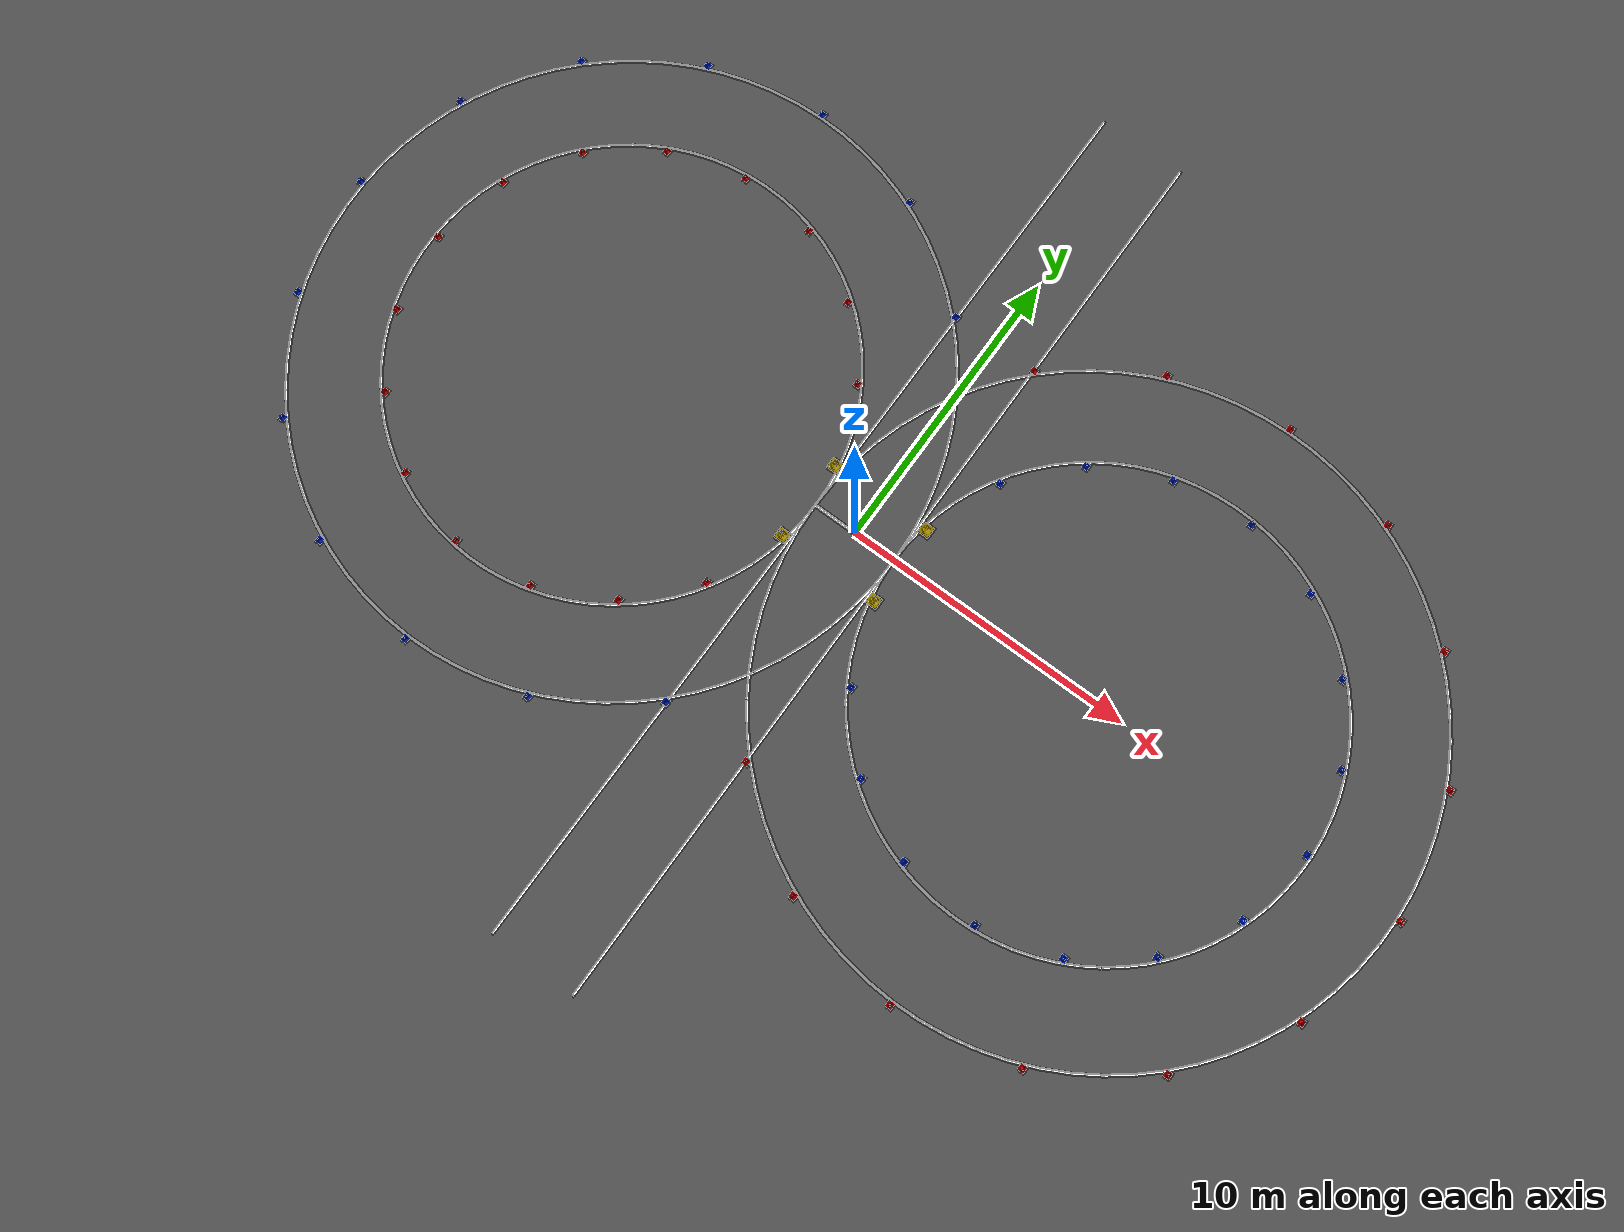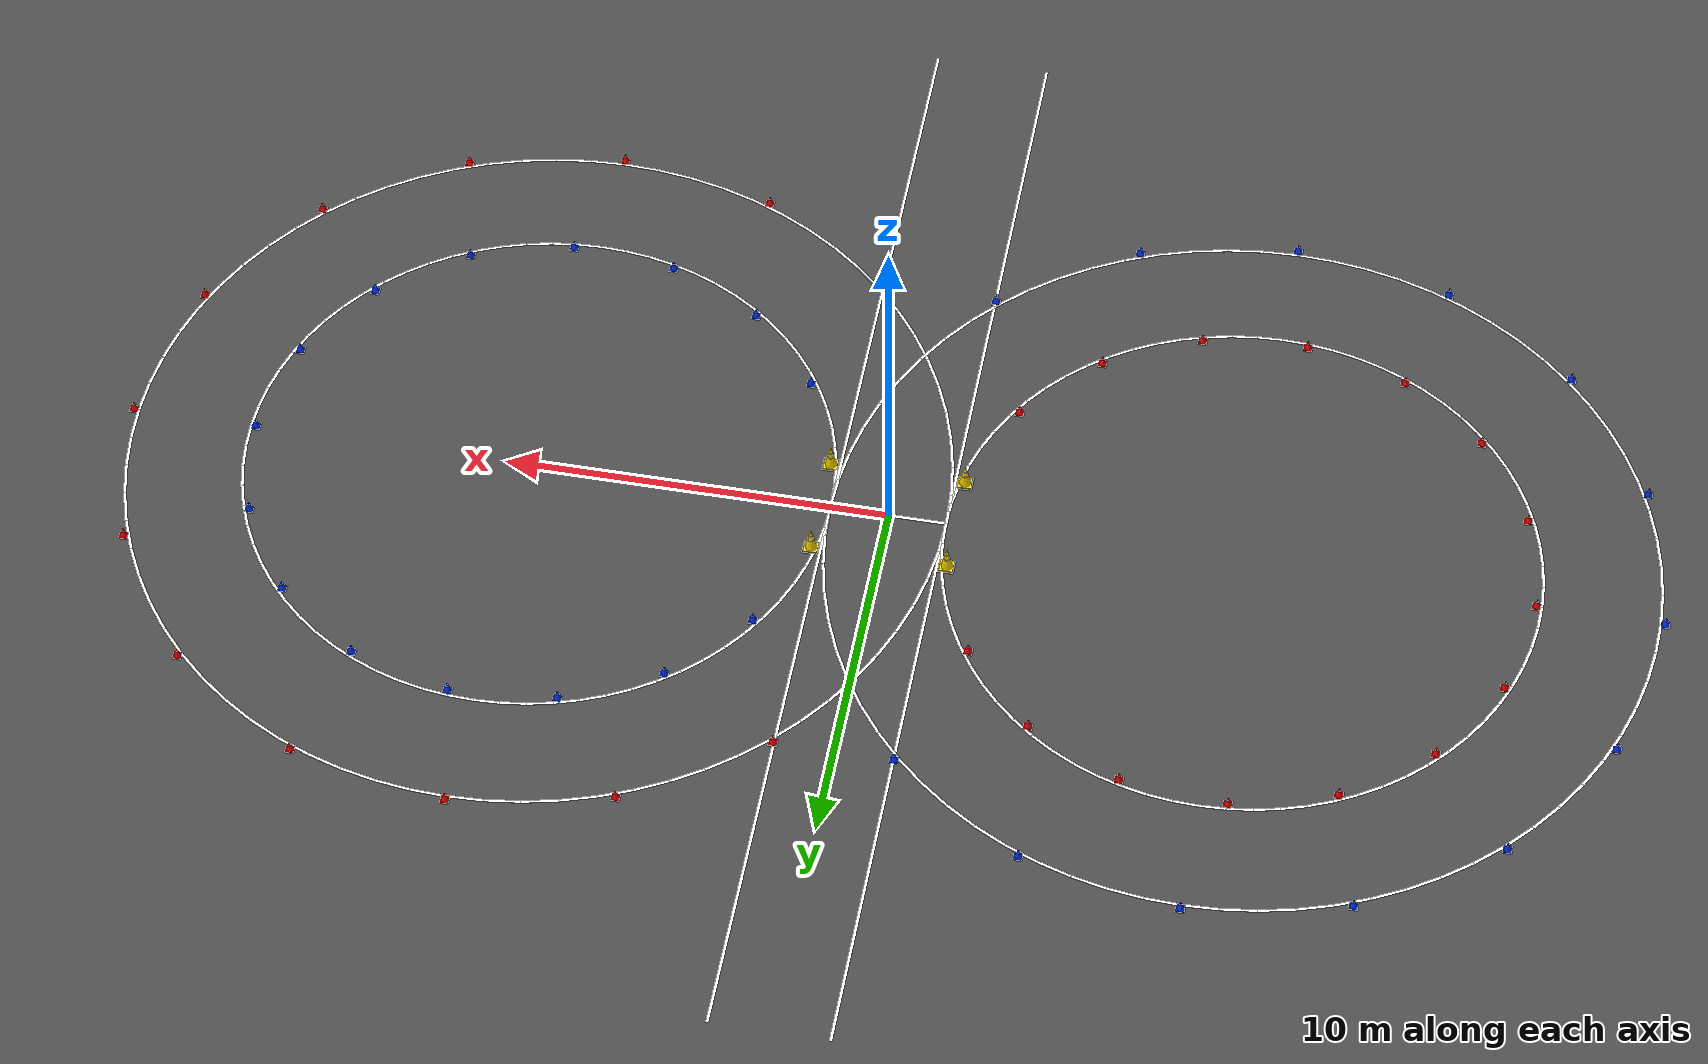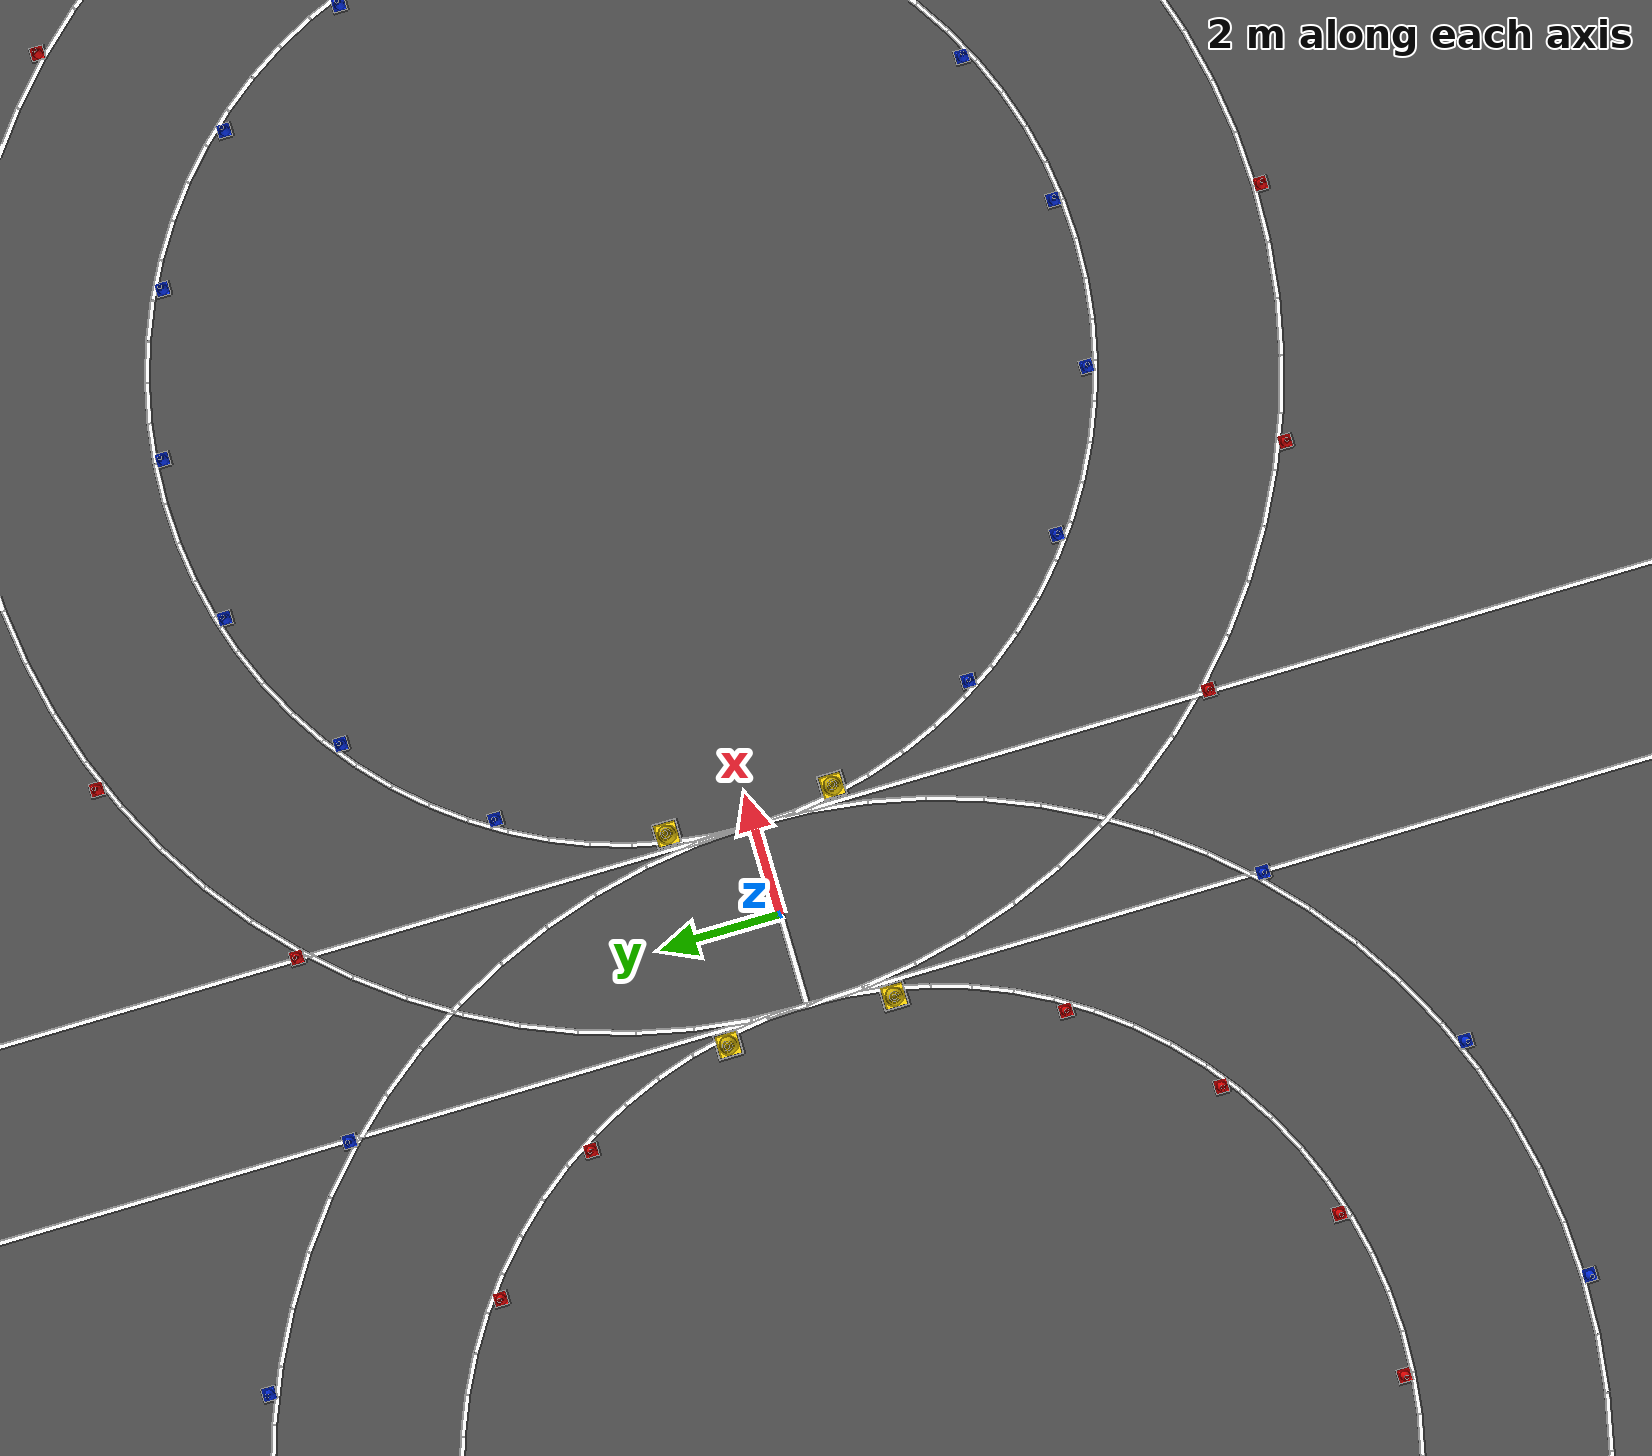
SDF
<?xml version="1.0"?>
<sdf version="1.9">
  <world name="skidpad">
    <physics name="default_physics" type="ignored">
      <max_step_size>0.001</max_step_size>
      <real_time_factor>1.0</real_time_factor>
    </physics>

    <plugin filename="gz-sim-physics-system" name="gz::sim::systems::Physics"/>
    <plugin filename="gz-sim-user-commands-system" name="gz::sim::systems::UserCommands"/>
    <plugin filename="gz-sim-scene-broadcaster-system" name="gz::sim::systems::SceneBroadcaster"/>
    <plugin filename="gz-sim-sensors-system" name="gz::sim::systems::Sensors">
      <render_engine>ogre2</render_engine>
    </plugin>

    <gui fullscreen="false">
      <plugin name="3D View" filename="GzScene3D">
        <gz-gui>
          <title>3D View</title>
          <property type="bool" key="showTitleBar">false</property>
          <property type="string" key="state">docked</property>
        </gz-gui>
        <engine>ogre2</engine>
        <scene>scene</scene>
        <!-- Start close to the racecar at the world origin. -->
        <camera_pose>-5 -5 4 0 0.45 0.7</camera_pose>
      </plugin>

      <plugin name="World control" filename="WorldControl">
        <gz-gui>
          <title>World control</title>
          <property type="bool" key="showTitleBar">false</property>
          <property type="bool" key="resizable">false</property>
          <property type="double" key="height">72</property>
          <property type="double" key="width">121</property>
          <property type="double" key="z">1</property>
          <property type="string" key="state">floating</property>
          <anchors target="3D View">
            <line own="left" target="left"/>
            <line own="bottom" target="bottom"/>
          </anchors>
        </gz-gui>
        <play_pause>true</play_pause>
        <step>true</step>
        <start_paused>false</start_paused>
      </plugin>

      <plugin name="World stats" filename="WorldStats">
        <gz-gui>
          <title>World stats</title>
          <property type="bool" key="showTitleBar">false</property>
          <property type="bool" key="resizable">false</property>
          <property type="double" key="height">110</property>
          <property type="double" key="width">290</property>
          <property type="double" key="z">1</property>
          <property type="string" key="state">floating</property>
          <anchors target="3D View">
            <line own="right" target="right"/>
            <line own="bottom" target="bottom"/>
          </anchors>
        </gz-gui>
        <sim_time>true</sim_time>
        <real_time>true</real_time>
        <real_time_factor>true</real_time_factor>
        <iterations>true</iterations>
      </plugin>

      <plugin name="Entity tree" filename="EntityTree"/>
    </gui>

    <scene>
      <ambient>0.6 0.6 0.6 1</ambient>
      <background>0.75 0.85 0.95 1</background>
      <shadows>true</shadows>
    </scene>

    <light type="directional" name="sun">
      <pose>0 0 30 0 0 0</pose>
      <cast_shadows>true</cast_shadows>
      <diffuse>0.9 0.9 0.9 1</diffuse>
      <specular>0.2 0.2 0.2 1</specular>
      <direction>-0.5 0.2 -0.9</direction>
    </light>

    <model name="ground_plane">
      <static>true</static>
      <link name="ground_link">
        <collision name="ground_collision">
          <geometry><plane><normal>0 0 1</normal><size>100 60</size></plane></geometry>
          <surface><friction><ode><mu>1.2</mu><mu2>1.0</mu2></ode></friction></surface>
        </collision>
        <visual name="ground_visual">
          <geometry><plane><normal>0 0 1</normal><size>100 60</size></plane></geometry>
          <material>
            <ambient>0.22 0.22 0.22 1</ambient>
            <diffuse>0.30 0.30 0.30 1</diffuse>
            <specular>0.05 0.05 0.05 1</specular>
          </material>
        </visual>
      </link>
    </model>

    <model name="skidpad_markings">
      <static>true</static>
      <link name="marking_link">
        <visual name="left_inner_boundary_01">
          <pose>-1.5073 0.3326 0.004 0 0 1.614430</pose>
          <geometry><box><size>0.6652 0.08 0.004</size></box></geometry>
          <material><ambient>0.95 0.95 0.95 1</ambient><diffuse>1 1 1 1</diffuse></material>
        </visual>
        <visual name="left_inner_boundary_02">
          <pose>-1.5652 0.9953 0.004 0 0 1.701696</pose>
          <geometry><box><size>0.6652 0.08 0.004</size></box></geometry>
          <material><ambient>0.95 0.95 0.95 1</ambient><diffuse>1 1 1 1</diffuse></material>
        </visual>
        <visual name="left_inner_boundary_03">
          <pose>-1.6807 1.6504 0.004 0 0 1.788962</pose>
          <geometry><box><size>0.6652 0.08 0.004</size></box></geometry>
          <material><ambient>0.95 0.95 0.95 1</ambient><diffuse>1 1 1 1</diffuse></material>
        </visual>
        <visual name="left_inner_boundary_04">
          <pose>-1.8529 2.2929 0.004 0 0 1.876229</pose>
          <geometry><box><size>0.6652 0.08 0.004</size></box></geometry>
          <material><ambient>0.95 0.95 0.95 1</ambient><diffuse>1 1 1 1</diffuse></material>
        </visual>
        <visual name="left_inner_boundary_05">
          <pose>-2.0804 2.9180 0.004 0 0 1.963495</pose>
          <geometry><box><size>0.6652 0.08 0.004</size></box></geometry>
          <material><ambient>0.95 0.95 0.95 1</ambient><diffuse>1 1 1 1</diffuse></material>
        </visual>
        <visual name="left_inner_boundary_06">
          <pose>-2.3615 3.5208 0.004 0 0 2.050762</pose>
          <geometry><box><size>0.6652 0.08 0.004</size></box></geometry>
          <material><ambient>0.95 0.95 0.95 1</ambient><diffuse>1 1 1 1</diffuse></material>
        </visual>
        <visual name="left_inner_boundary_07">
          <pose>-2.6941 4.0969 0.004 0 0 2.138028</pose>
          <geometry><box><size>0.6652 0.08 0.004</size></box></geometry>
          <material><ambient>0.95 0.95 0.95 1</ambient><diffuse>1 1 1 1</diffuse></material>
        </visual>
        <visual name="left_inner_boundary_08">
          <pose>-3.0757 4.6418 0.004 0 0 2.225295</pose>
          <geometry><box><size>0.6652 0.08 0.004</size></box></geometry>
          <material><ambient>0.95 0.95 0.95 1</ambient><diffuse>1 1 1 1</diffuse></material>
        </visual>
        <visual name="left_inner_boundary_09">
          <pose>-3.5033 5.1514 0.004 0 0 2.312561</pose>
          <geometry><box><size>0.6652 0.08 0.004</size></box></geometry>
          <material><ambient>0.95 0.95 0.95 1</ambient><diffuse>1 1 1 1</diffuse></material>
        </visual>
        <visual name="left_inner_boundary_10">
          <pose>-3.9736 5.6217 0.004 0 0 2.399828</pose>
          <geometry><box><size>0.6652 0.08 0.004</size></box></geometry>
          <material><ambient>0.95 0.95 0.95 1</ambient><diffuse>1 1 1 1</diffuse></material>
        </visual>
        <visual name="left_inner_boundary_11">
          <pose>-4.4832 6.0493 0.004 0 0 2.487094</pose>
          <geometry><box><size>0.6652 0.08 0.004</size></box></geometry>
          <material><ambient>0.95 0.95 0.95 1</ambient><diffuse>1 1 1 1</diffuse></material>
        </visual>
        <visual name="left_inner_boundary_12">
          <pose>-5.0281 6.4309 0.004 0 0 2.574361</pose>
          <geometry><box><size>0.6652 0.08 0.004</size></box></geometry>
          <material><ambient>0.95 0.95 0.95 1</ambient><diffuse>1 1 1 1</diffuse></material>
        </visual>
        <visual name="left_inner_boundary_13">
          <pose>-5.6042 6.7635 0.004 0 0 2.661627</pose>
          <geometry><box><size>0.6652 0.08 0.004</size></box></geometry>
          <material><ambient>0.95 0.95 0.95 1</ambient><diffuse>1 1 1 1</diffuse></material>
        </visual>
        <visual name="left_inner_boundary_14">
          <pose>-6.2070 7.0446 0.004 0 0 2.748894</pose>
          <geometry><box><size>0.6652 0.08 0.004</size></box></geometry>
          <material><ambient>0.95 0.95 0.95 1</ambient><diffuse>1 1 1 1</diffuse></material>
        </visual>
        <visual name="left_inner_boundary_15">
          <pose>-6.8321 7.2721 0.004 0 0 2.836160</pose>
          <geometry><box><size>0.6652 0.08 0.004</size></box></geometry>
          <material><ambient>0.95 0.95 0.95 1</ambient><diffuse>1 1 1 1</diffuse></material>
        </visual>
        <visual name="left_inner_boundary_16">
          <pose>-7.4746 7.4443 0.004 0 0 2.923426</pose>
          <geometry><box><size>0.6652 0.08 0.004</size></box></geometry>
          <material><ambient>0.95 0.95 0.95 1</ambient><diffuse>1 1 1 1</diffuse></material>
        </visual>
        <visual name="left_inner_boundary_17">
          <pose>-8.1297 7.5598 0.004 0 0 3.010693</pose>
          <geometry><box><size>0.6652 0.08 0.004</size></box></geometry>
          <material><ambient>0.95 0.95 0.95 1</ambient><diffuse>1 1 1 1</diffuse></material>
        </visual>
        <visual name="left_inner_boundary_18">
          <pose>-8.7924 7.6177 0.004 0 0 3.097959</pose>
          <geometry><box><size>0.6652 0.08 0.004</size></box></geometry>
          <material><ambient>0.95 0.95 0.95 1</ambient><diffuse>1 1 1 1</diffuse></material>
        </visual>
        <visual name="left_inner_boundary_19">
          <pose>-9.4576 7.6177 0.004 0 0 3.185226</pose>
          <geometry><box><size>0.6652 0.08 0.004</size></box></geometry>
          <material><ambient>0.95 0.95 0.95 1</ambient><diffuse>1 1 1 1</diffuse></material>
        </visual>
        <visual name="left_inner_boundary_20">
          <pose>-10.1203 7.5598 0.004 0 0 3.272492</pose>
          <geometry><box><size>0.6652 0.08 0.004</size></box></geometry>
          <material><ambient>0.95 0.95 0.95 1</ambient><diffuse>1 1 1 1</diffuse></material>
        </visual>
        <visual name="left_inner_boundary_21">
          <pose>-10.7754 7.4443 0.004 0 0 3.359759</pose>
          <geometry><box><size>0.6652 0.08 0.004</size></box></geometry>
          <material><ambient>0.95 0.95 0.95 1</ambient><diffuse>1 1 1 1</diffuse></material>
        </visual>
        <visual name="left_inner_boundary_22">
          <pose>-11.4179 7.2721 0.004 0 0 3.447025</pose>
          <geometry><box><size>0.6652 0.08 0.004</size></box></geometry>
          <material><ambient>0.95 0.95 0.95 1</ambient><diffuse>1 1 1 1</diffuse></material>
        </visual>
        <visual name="left_inner_boundary_23">
          <pose>-12.0430 7.0446 0.004 0 0 3.534292</pose>
          <geometry><box><size>0.6652 0.08 0.004</size></box></geometry>
          <material><ambient>0.95 0.95 0.95 1</ambient><diffuse>1 1 1 1</diffuse></material>
        </visual>
        <visual name="left_inner_boundary_24">
          <pose>-12.6458 6.7635 0.004 0 0 3.621558</pose>
          <geometry><box><size>0.6652 0.08 0.004</size></box></geometry>
          <material><ambient>0.95 0.95 0.95 1</ambient><diffuse>1 1 1 1</diffuse></material>
        </visual>
        <visual name="left_inner_boundary_25">
          <pose>-13.2219 6.4309 0.004 0 0 3.708825</pose>
          <geometry><box><size>0.6652 0.08 0.004</size></box></geometry>
          <material><ambient>0.95 0.95 0.95 1</ambient><diffuse>1 1 1 1</diffuse></material>
        </visual>
        <visual name="left_inner_boundary_26">
          <pose>-13.7668 6.0493 0.004 0 0 3.796091</pose>
          <geometry><box><size>0.6652 0.08 0.004</size></box></geometry>
          <material><ambient>0.95 0.95 0.95 1</ambient><diffuse>1 1 1 1</diffuse></material>
        </visual>
        <visual name="left_inner_boundary_27">
          <pose>-14.2764 5.6217 0.004 0 0 3.883358</pose>
          <geometry><box><size>0.6652 0.08 0.004</size></box></geometry>
          <material><ambient>0.95 0.95 0.95 1</ambient><diffuse>1 1 1 1</diffuse></material>
        </visual>
        <visual name="left_inner_boundary_28">
          <pose>-14.7467 5.1514 0.004 0 0 3.970624</pose>
          <geometry><box><size>0.6652 0.08 0.004</size></box></geometry>
          <material><ambient>0.95 0.95 0.95 1</ambient><diffuse>1 1 1 1</diffuse></material>
        </visual>
        <visual name="left_inner_boundary_29">
          <pose>-15.1743 4.6418 0.004 0 0 4.057891</pose>
          <geometry><box><size>0.6652 0.08 0.004</size></box></geometry>
          <material><ambient>0.95 0.95 0.95 1</ambient><diffuse>1 1 1 1</diffuse></material>
        </visual>
        <visual name="left_inner_boundary_30">
          <pose>-15.5559 4.0969 0.004 0 0 4.145157</pose>
          <geometry><box><size>0.6652 0.08 0.004</size></box></geometry>
          <material><ambient>0.95 0.95 0.95 1</ambient><diffuse>1 1 1 1</diffuse></material>
        </visual>
        <visual name="left_inner_boundary_31">
          <pose>-15.8885 3.5208 0.004 0 0 4.232423</pose>
          <geometry><box><size>0.6652 0.08 0.004</size></box></geometry>
          <material><ambient>0.95 0.95 0.95 1</ambient><diffuse>1 1 1 1</diffuse></material>
        </visual>
        <visual name="left_inner_boundary_32">
          <pose>-16.1696 2.9180 0.004 0 0 4.319690</pose>
          <geometry><box><size>0.6652 0.08 0.004</size></box></geometry>
          <material><ambient>0.95 0.95 0.95 1</ambient><diffuse>1 1 1 1</diffuse></material>
        </visual>
        <visual name="left_inner_boundary_33">
          <pose>-16.3971 2.2929 0.004 0 0 4.406956</pose>
          <geometry><box><size>0.6652 0.08 0.004</size></box></geometry>
          <material><ambient>0.95 0.95 0.95 1</ambient><diffuse>1 1 1 1</diffuse></material>
        </visual>
        <visual name="left_inner_boundary_34">
          <pose>-16.5693 1.6504 0.004 0 0 4.494223</pose>
          <geometry><box><size>0.6652 0.08 0.004</size></box></geometry>
          <material><ambient>0.95 0.95 0.95 1</ambient><diffuse>1 1 1 1</diffuse></material>
        </visual>
        <visual name="left_inner_boundary_35">
          <pose>-16.6848 0.9953 0.004 0 0 4.581489</pose>
          <geometry><box><size>0.6652 0.08 0.004</size></box></geometry>
          <material><ambient>0.95 0.95 0.95 1</ambient><diffuse>1 1 1 1</diffuse></material>
        </visual>
        <visual name="left_inner_boundary_36">
          <pose>-16.7427 0.3326 0.004 0 0 4.668756</pose>
          <geometry><box><size>0.6652 0.08 0.004</size></box></geometry>
          <material><ambient>0.95 0.95 0.95 1</ambient><diffuse>1 1 1 1</diffuse></material>
        </visual>
        <visual name="left_inner_boundary_37">
          <pose>-16.7427 -0.3326 0.004 0 0 4.756022</pose>
          <geometry><box><size>0.6652 0.08 0.004</size></box></geometry>
          <material><ambient>0.95 0.95 0.95 1</ambient><diffuse>1 1 1 1</diffuse></material>
        </visual>
        <visual name="left_inner_boundary_38">
          <pose>-16.6848 -0.9953 0.004 0 0 4.843289</pose>
          <geometry><box><size>0.6652 0.08 0.004</size></box></geometry>
          <material><ambient>0.95 0.95 0.95 1</ambient><diffuse>1 1 1 1</diffuse></material>
        </visual>
        <visual name="left_inner_boundary_39">
          <pose>-16.5693 -1.6504 0.004 0 0 4.930555</pose>
          <geometry><box><size>0.6652 0.08 0.004</size></box></geometry>
          <material><ambient>0.95 0.95 0.95 1</ambient><diffuse>1 1 1 1</diffuse></material>
        </visual>
        <visual name="left_inner_boundary_40">
          <pose>-16.3971 -2.2929 0.004 0 0 5.017822</pose>
          <geometry><box><size>0.6652 0.08 0.004</size></box></geometry>
          <material><ambient>0.95 0.95 0.95 1</ambient><diffuse>1 1 1 1</diffuse></material>
        </visual>
        <visual name="left_inner_boundary_41">
          <pose>-16.1696 -2.9180 0.004 0 0 5.105088</pose>
          <geometry><box><size>0.6652 0.08 0.004</size></box></geometry>
          <material><ambient>0.95 0.95 0.95 1</ambient><diffuse>1 1 1 1</diffuse></material>
        </visual>
        <visual name="left_inner_boundary_42">
          <pose>-15.8885 -3.5208 0.004 0 0 5.192355</pose>
          <geometry><box><size>0.6652 0.08 0.004</size></box></geometry>
          <material><ambient>0.95 0.95 0.95 1</ambient><diffuse>1 1 1 1</diffuse></material>
        </visual>
        <visual name="left_inner_boundary_43">
          <pose>-15.5559 -4.0969 0.004 0 0 5.279621</pose>
          <geometry><box><size>0.6652 0.08 0.004</size></box></geometry>
          <material><ambient>0.95 0.95 0.95 1</ambient><diffuse>1 1 1 1</diffuse></material>
        </visual>
        <visual name="left_inner_boundary_44">
          <pose>-15.1743 -4.6418 0.004 0 0 5.366887</pose>
          <geometry><box><size>0.6652 0.08 0.004</size></box></geometry>
          <material><ambient>0.95 0.95 0.95 1</ambient><diffuse>1 1 1 1</diffuse></material>
        </visual>
        <visual name="left_inner_boundary_45">
          <pose>-14.7467 -5.1514 0.004 0 0 5.454154</pose>
          <geometry><box><size>0.6652 0.08 0.004</size></box></geometry>
          <material><ambient>0.95 0.95 0.95 1</ambient><diffuse>1 1 1 1</diffuse></material>
        </visual>
        <visual name="left_inner_boundary_46">
          <pose>-14.2764 -5.6217 0.004 0 0 5.541420</pose>
          <geometry><box><size>0.6652 0.08 0.004</size></box></geometry>
          <material><ambient>0.95 0.95 0.95 1</ambient><diffuse>1 1 1 1</diffuse></material>
        </visual>
        <visual name="left_inner_boundary_47">
          <pose>-13.7668 -6.0493 0.004 0 0 5.628687</pose>
          <geometry><box><size>0.6652 0.08 0.004</size></box></geometry>
          <material><ambient>0.95 0.95 0.95 1</ambient><diffuse>1 1 1 1</diffuse></material>
        </visual>
        <visual name="left_inner_boundary_48">
          <pose>-13.2219 -6.4309 0.004 0 0 5.715953</pose>
          <geometry><box><size>0.6652 0.08 0.004</size></box></geometry>
          <material><ambient>0.95 0.95 0.95 1</ambient><diffuse>1 1 1 1</diffuse></material>
        </visual>
        <visual name="left_inner_boundary_49">
          <pose>-12.6458 -6.7635 0.004 0 0 5.803220</pose>
          <geometry><box><size>0.6652 0.08 0.004</size></box></geometry>
          <material><ambient>0.95 0.95 0.95 1</ambient><diffuse>1 1 1 1</diffuse></material>
        </visual>
        <visual name="left_inner_boundary_50">
          <pose>-12.0430 -7.0446 0.004 0 0 5.890486</pose>
          <geometry><box><size>0.6652 0.08 0.004</size></box></geometry>
          <material><ambient>0.95 0.95 0.95 1</ambient><diffuse>1 1 1 1</diffuse></material>
        </visual>
        <visual name="left_inner_boundary_51">
          <pose>-11.4179 -7.2721 0.004 0 0 5.977753</pose>
          <geometry><box><size>0.6652 0.08 0.004</size></box></geometry>
          <material><ambient>0.95 0.95 0.95 1</ambient><diffuse>1 1 1 1</diffuse></material>
        </visual>
        <visual name="left_inner_boundary_52">
          <pose>-10.7754 -7.4443 0.004 0 0 6.065019</pose>
          <geometry><box><size>0.6652 0.08 0.004</size></box></geometry>
          <material><ambient>0.95 0.95 0.95 1</ambient><diffuse>1 1 1 1</diffuse></material>
        </visual>
        <visual name="left_inner_boundary_53">
          <pose>-10.1203 -7.5598 0.004 0 0 6.152286</pose>
          <geometry><box><size>0.6652 0.08 0.004</size></box></geometry>
          <material><ambient>0.95 0.95 0.95 1</ambient><diffuse>1 1 1 1</diffuse></material>
        </visual>
        <visual name="left_inner_boundary_54">
          <pose>-9.4576 -7.6177 0.004 0 0 6.239552</pose>
          <geometry><box><size>0.6652 0.08 0.004</size></box></geometry>
          <material><ambient>0.95 0.95 0.95 1</ambient><diffuse>1 1 1 1</diffuse></material>
        </visual>
        <visual name="left_inner_boundary_55">
          <pose>-8.7924 -7.6177 0.004 0 0 6.326819</pose>
          <geometry><box><size>0.6652 0.08 0.004</size></box></geometry>
          <material><ambient>0.95 0.95 0.95 1</ambient><diffuse>1 1 1 1</diffuse></material>
        </visual>
        <visual name="left_inner_boundary_56">
          <pose>-8.1297 -7.5598 0.004 0 0 6.414085</pose>
          <geometry><box><size>0.6652 0.08 0.004</size></box></geometry>
          <material><ambient>0.95 0.95 0.95 1</ambient><diffuse>1 1 1 1</diffuse></material>
        </visual>
        <visual name="left_inner_boundary_57">
          <pose>-7.4746 -7.4443 0.004 0 0 6.501351</pose>
          <geometry><box><size>0.6652 0.08 0.004</size></box></geometry>
          <material><ambient>0.95 0.95 0.95 1</ambient><diffuse>1 1 1 1</diffuse></material>
        </visual>
        <visual name="left_inner_boundary_58">
          <pose>-6.8321 -7.2721 0.004 0 0 6.588618</pose>
          <geometry><box><size>0.6652 0.08 0.004</size></box></geometry>
          <material><ambient>0.95 0.95 0.95 1</ambient><diffuse>1 1 1 1</diffuse></material>
        </visual>
        <visual name="left_inner_boundary_59">
          <pose>-6.2070 -7.0446 0.004 0 0 6.675884</pose>
          <geometry><box><size>0.6652 0.08 0.004</size></box></geometry>
          <material><ambient>0.95 0.95 0.95 1</ambient><diffuse>1 1 1 1</diffuse></material>
        </visual>
        <visual name="left_inner_boundary_60">
          <pose>-5.6042 -6.7635 0.004 0 0 6.763151</pose>
          <geometry><box><size>0.6652 0.08 0.004</size></box></geometry>
          <material><ambient>0.95 0.95 0.95 1</ambient><diffuse>1 1 1 1</diffuse></material>
        </visual>
        <visual name="left_inner_boundary_61">
          <pose>-5.0281 -6.4309 0.004 0 0 6.850417</pose>
          <geometry><box><size>0.6652 0.08 0.004</size></box></geometry>
          <material><ambient>0.95 0.95 0.95 1</ambient><diffuse>1 1 1 1</diffuse></material>
        </visual>
        <visual name="left_inner_boundary_62">
          <pose>-4.4832 -6.0493 0.004 0 0 6.937684</pose>
          <geometry><box><size>0.6652 0.08 0.004</size></box></geometry>
          <material><ambient>0.95 0.95 0.95 1</ambient><diffuse>1 1 1 1</diffuse></material>
        </visual>
        <visual name="left_inner_boundary_63">
          <pose>-3.9736 -5.6217 0.004 0 0 7.024950</pose>
          <geometry><box><size>0.6652 0.08 0.004</size></box></geometry>
          <material><ambient>0.95 0.95 0.95 1</ambient><diffuse>1 1 1 1</diffuse></material>
        </visual>
        <visual name="left_inner_boundary_64">
          <pose>-3.5033 -5.1514 0.004 0 0 7.112217</pose>
          <geometry><box><size>0.6652 0.08 0.004</size></box></geometry>
          <material><ambient>0.95 0.95 0.95 1</ambient><diffuse>1 1 1 1</diffuse></material>
        </visual>
        <visual name="left_inner_boundary_65">
          <pose>-3.0757 -4.6418 0.004 0 0 7.199483</pose>
          <geometry><box><size>0.6652 0.08 0.004</size></box></geometry>
          <material><ambient>0.95 0.95 0.95 1</ambient><diffuse>1 1 1 1</diffuse></material>
        </visual>
        <visual name="left_inner_boundary_66">
          <pose>-2.6941 -4.0969 0.004 0 0 7.286750</pose>
          <geometry><box><size>0.6652 0.08 0.004</size></box></geometry>
          <material><ambient>0.95 0.95 0.95 1</ambient><diffuse>1 1 1 1</diffuse></material>
        </visual>
        <visual name="left_inner_boundary_67">
          <pose>-2.3615 -3.5208 0.004 0 0 7.374016</pose>
          <geometry><box><size>0.6652 0.08 0.004</size></box></geometry>
          <material><ambient>0.95 0.95 0.95 1</ambient><diffuse>1 1 1 1</diffuse></material>
        </visual>
        <visual name="left_inner_boundary_68">
          <pose>-2.0804 -2.9180 0.004 0 0 7.461283</pose>
          <geometry><box><size>0.6652 0.08 0.004</size></box></geometry>
          <material><ambient>0.95 0.95 0.95 1</ambient><diffuse>1 1 1 1</diffuse></material>
        </visual>
        <visual name="left_inner_boundary_69">
          <pose>-1.8529 -2.2929 0.004 0 0 7.548549</pose>
          <geometry><box><size>0.6652 0.08 0.004</size></box></geometry>
          <material><ambient>0.95 0.95 0.95 1</ambient><diffuse>1 1 1 1</diffuse></material>
        </visual>
        <visual name="left_inner_boundary_70">
          <pose>-1.6807 -1.6504 0.004 0 0 7.635815</pose>
          <geometry><box><size>0.6652 0.08 0.004</size></box></geometry>
          <material><ambient>0.95 0.95 0.95 1</ambient><diffuse>1 1 1 1</diffuse></material>
        </visual>
        <visual name="left_inner_boundary_71">
          <pose>-1.5652 -0.9953 0.004 0 0 7.723082</pose>
          <geometry><box><size>0.6652 0.08 0.004</size></box></geometry>
          <material><ambient>0.95 0.95 0.95 1</ambient><diffuse>1 1 1 1</diffuse></material>
        </visual>
        <visual name="left_inner_boundary_72">
          <pose>-1.5073 -0.3326 0.004 0 0 7.810348</pose>
          <geometry><box><size>0.6652 0.08 0.004</size></box></geometry>
          <material><ambient>0.95 0.95 0.95 1</ambient><diffuse>1 1 1 1</diffuse></material>
        </visual>
        <visual name="left_outer_boundary_01">
          <pose>1.4899 0.4635 0.004 0 0 1.614430</pose>
          <geometry><box><size>0.9269 0.08 0.004</size></box></geometry>
          <material><ambient>0.95 0.95 0.95 1</ambient><diffuse>1 1 1 1</diffuse></material>
        </visual>
        <visual name="left_outer_boundary_02">
          <pose>1.4091 1.3868 0.004 0 0 1.701696</pose>
          <geometry><box><size>0.9269 0.08 0.004</size></box></geometry>
          <material><ambient>0.95 0.95 0.95 1</ambient><diffuse>1 1 1 1</diffuse></material>
        </visual>
        <visual name="left_outer_boundary_03">
          <pose>1.2481 2.2997 0.004 0 0 1.788962</pose>
          <geometry><box><size>0.9269 0.08 0.004</size></box></geometry>
          <material><ambient>0.95 0.95 0.95 1</ambient><diffuse>1 1 1 1</diffuse></material>
        </visual>
        <visual name="left_outer_boundary_04">
          <pose>1.0082 3.1950 0.004 0 0 1.876229</pose>
          <geometry><box><size>0.9269 0.08 0.004</size></box></geometry>
          <material><ambient>0.95 0.95 0.95 1</ambient><diffuse>1 1 1 1</diffuse></material>
        </visual>
        <visual name="left_outer_boundary_05">
          <pose>0.6912 4.0660 0.004 0 0 1.963495</pose>
          <geometry><box><size>0.9269 0.08 0.004</size></box></geometry>
          <material><ambient>0.95 0.95 0.95 1</ambient><diffuse>1 1 1 1</diffuse></material>
        </visual>
        <visual name="left_outer_boundary_06">
          <pose>0.2995 4.9061 0.004 0 0 2.050762</pose>
          <geometry><box><size>0.9269 0.08 0.004</size></box></geometry>
          <material><ambient>0.95 0.95 0.95 1</ambient><diffuse>1 1 1 1</diffuse></material>
        </visual>
        <visual name="left_outer_boundary_07">
          <pose>-0.1640 5.7088 0.004 0 0 2.138028</pose>
          <geometry><box><size>0.9269 0.08 0.004</size></box></geometry>
          <material><ambient>0.95 0.95 0.95 1</ambient><diffuse>1 1 1 1</diffuse></material>
        </visual>
        <visual name="left_outer_boundary_08">
          <pose>-0.6956 6.4681 0.004 0 0 2.225295</pose>
          <geometry><box><size>0.9269 0.08 0.004</size></box></geometry>
          <material><ambient>0.95 0.95 0.95 1</ambient><diffuse>1 1 1 1</diffuse></material>
        </visual>
        <visual name="left_outer_boundary_09">
          <pose>-1.2914 7.1781 0.004 0 0 2.312561</pose>
          <geometry><box><size>0.9269 0.08 0.004</size></box></geometry>
          <material><ambient>0.95 0.95 0.95 1</ambient><diffuse>1 1 1 1</diffuse></material>
        </visual>
        <visual name="left_outer_boundary_10">
          <pose>-1.9469 7.8336 0.004 0 0 2.399828</pose>
          <geometry><box><size>0.9269 0.08 0.004</size></box></geometry>
          <material><ambient>0.95 0.95 0.95 1</ambient><diffuse>1 1 1 1</diffuse></material>
        </visual>
        <visual name="left_outer_boundary_11">
          <pose>-2.6569 8.4294 0.004 0 0 2.487094</pose>
          <geometry><box><size>0.9269 0.08 0.004</size></box></geometry>
          <material><ambient>0.95 0.95 0.95 1</ambient><diffuse>1 1 1 1</diffuse></material>
        </visual>
        <visual name="left_outer_boundary_12">
          <pose>-3.4162 8.9610 0.004 0 0 2.574361</pose>
          <geometry><box><size>0.9269 0.08 0.004</size></box></geometry>
          <material><ambient>0.95 0.95 0.95 1</ambient><diffuse>1 1 1 1</diffuse></material>
        </visual>
        <visual name="left_outer_boundary_13">
          <pose>-4.2189 9.4245 0.004 0 0 2.661627</pose>
          <geometry><box><size>0.9269 0.08 0.004</size></box></geometry>
          <material><ambient>0.95 0.95 0.95 1</ambient><diffuse>1 1 1 1</diffuse></material>
        </visual>
        <visual name="left_outer_boundary_14">
          <pose>-5.0590 9.8162 0.004 0 0 2.748894</pose>
          <geometry><box><size>0.9269 0.08 0.004</size></box></geometry>
          <material><ambient>0.95 0.95 0.95 1</ambient><diffuse>1 1 1 1</diffuse></material>
        </visual>
        <visual name="left_outer_boundary_15">
          <pose>-5.9300 10.1332 0.004 0 0 2.836160</pose>
          <geometry><box><size>0.9269 0.08 0.004</size></box></geometry>
          <material><ambient>0.95 0.95 0.95 1</ambient><diffuse>1 1 1 1</diffuse></material>
        </visual>
        <visual name="left_outer_boundary_16">
          <pose>-6.8253 10.3731 0.004 0 0 2.923426</pose>
          <geometry><box><size>0.9269 0.08 0.004</size></box></geometry>
          <material><ambient>0.95 0.95 0.95 1</ambient><diffuse>1 1 1 1</diffuse></material>
        </visual>
        <visual name="left_outer_boundary_17">
          <pose>-7.7382 10.5341 0.004 0 0 3.010693</pose>
          <geometry><box><size>0.9269 0.08 0.004</size></box></geometry>
          <material><ambient>0.95 0.95 0.95 1</ambient><diffuse>1 1 1 1</diffuse></material>
        </visual>
        <visual name="left_outer_boundary_18">
          <pose>-8.6615 10.6149 0.004 0 0 3.097959</pose>
          <geometry><box><size>0.9269 0.08 0.004</size></box></geometry>
          <material><ambient>0.95 0.95 0.95 1</ambient><diffuse>1 1 1 1</diffuse></material>
        </visual>
        <visual name="left_outer_boundary_19">
          <pose>-9.5885 10.6149 0.004 0 0 3.185226</pose>
          <geometry><box><size>0.9269 0.08 0.004</size></box></geometry>
          <material><ambient>0.95 0.95 0.95 1</ambient><diffuse>1 1 1 1</diffuse></material>
        </visual>
        <visual name="left_outer_boundary_20">
          <pose>-10.5118 10.5341 0.004 0 0 3.272492</pose>
          <geometry><box><size>0.9269 0.08 0.004</size></box></geometry>
          <material><ambient>0.95 0.95 0.95 1</ambient><diffuse>1 1 1 1</diffuse></material>
        </visual>
        <visual name="left_outer_boundary_21">
          <pose>-11.4247 10.3731 0.004 0 0 3.359759</pose>
          <geometry><box><size>0.9269 0.08 0.004</size></box></geometry>
          <material><ambient>0.95 0.95 0.95 1</ambient><diffuse>1 1 1 1</diffuse></material>
        </visual>
        <visual name="left_outer_boundary_22">
          <pose>-12.3200 10.1332 0.004 0 0 3.447025</pose>
          <geometry><box><size>0.9269 0.08 0.004</size></box></geometry>
          <material><ambient>0.95 0.95 0.95 1</ambient><diffuse>1 1 1 1</diffuse></material>
        </visual>
        <visual name="left_outer_boundary_23">
          <pose>-13.1910 9.8162 0.004 0 0 3.534292</pose>
          <geometry><box><size>0.9269 0.08 0.004</size></box></geometry>
          <material><ambient>0.95 0.95 0.95 1</ambient><diffuse>1 1 1 1</diffuse></material>
        </visual>
        <visual name="left_outer_boundary_24">
          <pose>-14.0311 9.4245 0.004 0 0 3.621558</pose>
          <geometry><box><size>0.9269 0.08 0.004</size></box></geometry>
          <material><ambient>0.95 0.95 0.95 1</ambient><diffuse>1 1 1 1</diffuse></material>
        </visual>
        <visual name="left_outer_boundary_25">
          <pose>-14.8338 8.9610 0.004 0 0 3.708825</pose>
          <geometry><box><size>0.9269 0.08 0.004</size></box></geometry>
          <material><ambient>0.95 0.95 0.95 1</ambient><diffuse>1 1 1 1</diffuse></material>
        </visual>
        <visual name="left_outer_boundary_26">
          <pose>-15.5931 8.4294 0.004 0 0 3.796091</pose>
          <geometry><box><size>0.9269 0.08 0.004</size></box></geometry>
          <material><ambient>0.95 0.95 0.95 1</ambient><diffuse>1 1 1 1</diffuse></material>
        </visual>
        <visual name="left_outer_boundary_27">
          <pose>-16.3031 7.8336 0.004 0 0 3.883358</pose>
          <geometry><box><size>0.9269 0.08 0.004</size></box></geometry>
          <material><ambient>0.95 0.95 0.95 1</ambient><diffuse>1 1 1 1</diffuse></material>
        </visual>
        <visual name="left_outer_boundary_28">
          <pose>-16.9586 7.1781 0.004 0 0 3.970624</pose>
          <geometry><box><size>0.9269 0.08 0.004</size></box></geometry>
          <material><ambient>0.95 0.95 0.95 1</ambient><diffuse>1 1 1 1</diffuse></material>
        </visual>
        <visual name="left_outer_boundary_29">
          <pose>-17.5544 6.4681 0.004 0 0 4.057891</pose>
          <geometry><box><size>0.9269 0.08 0.004</size></box></geometry>
          <material><ambient>0.95 0.95 0.95 1</ambient><diffuse>1 1 1 1</diffuse></material>
        </visual>
        <visual name="left_outer_boundary_30">
          <pose>-18.0860 5.7088 0.004 0 0 4.145157</pose>
          <geometry><box><size>0.9269 0.08 0.004</size></box></geometry>
          <material><ambient>0.95 0.95 0.95 1</ambient><diffuse>1 1 1 1</diffuse></material>
        </visual>
        <visual name="left_outer_boundary_31">
          <pose>-18.5495 4.9061 0.004 0 0 4.232423</pose>
          <geometry><box><size>0.9269 0.08 0.004</size></box></geometry>
          <material><ambient>0.95 0.95 0.95 1</ambient><diffuse>1 1 1 1</diffuse></material>
        </visual>
        <visual name="left_outer_boundary_32">
          <pose>-18.9412 4.0660 0.004 0 0 4.319690</pose>
          <geometry><box><size>0.9269 0.08 0.004</size></box></geometry>
          <material><ambient>0.95 0.95 0.95 1</ambient><diffuse>1 1 1 1</diffuse></material>
        </visual>
        <visual name="left_outer_boundary_33">
          <pose>-19.2582 3.1950 0.004 0 0 4.406956</pose>
          <geometry><box><size>0.9269 0.08 0.004</size></box></geometry>
          <material><ambient>0.95 0.95 0.95 1</ambient><diffuse>1 1 1 1</diffuse></material>
        </visual>
        <visual name="left_outer_boundary_34">
          <pose>-19.4981 2.2997 0.004 0 0 4.494223</pose>
          <geometry><box><size>0.9269 0.08 0.004</size></box></geometry>
          <material><ambient>0.95 0.95 0.95 1</ambient><diffuse>1 1 1 1</diffuse></material>
        </visual>
        <visual name="left_outer_boundary_35">
          <pose>-19.6591 1.3868 0.004 0 0 4.581489</pose>
          <geometry><box><size>0.9269 0.08 0.004</size></box></geometry>
          <material><ambient>0.95 0.95 0.95 1</ambient><diffuse>1 1 1 1</diffuse></material>
        </visual>
        <visual name="left_outer_boundary_36">
          <pose>-19.7399 0.4635 0.004 0 0 4.668756</pose>
          <geometry><box><size>0.9269 0.08 0.004</size></box></geometry>
          <material><ambient>0.95 0.95 0.95 1</ambient><diffuse>1 1 1 1</diffuse></material>
        </visual>
        <visual name="left_outer_boundary_37">
          <pose>-19.7399 -0.4635 0.004 0 0 4.756022</pose>
          <geometry><box><size>0.9269 0.08 0.004</size></box></geometry>
          <material><ambient>0.95 0.95 0.95 1</ambient><diffuse>1 1 1 1</diffuse></material>
        </visual>
        <visual name="left_outer_boundary_38">
          <pose>-19.6591 -1.3868 0.004 0 0 4.843289</pose>
          <geometry><box><size>0.9269 0.08 0.004</size></box></geometry>
          <material><ambient>0.95 0.95 0.95 1</ambient><diffuse>1 1 1 1</diffuse></material>
        </visual>
        <visual name="left_outer_boundary_39">
          <pose>-19.4981 -2.2997 0.004 0 0 4.930555</pose>
          <geometry><box><size>0.9269 0.08 0.004</size></box></geometry>
          <material><ambient>0.95 0.95 0.95 1</ambient><diffuse>1 1 1 1</diffuse></material>
        </visual>
        <visual name="left_outer_boundary_40">
          <pose>-19.2582 -3.1950 0.004 0 0 5.017822</pose>
          <geometry><box><size>0.9269 0.08 0.004</size></box></geometry>
          <material><ambient>0.95 0.95 0.95 1</ambient><diffuse>1 1 1 1</diffuse></material>
        </visual>
        <visual name="left_outer_boundary_41">
          <pose>-18.9412 -4.0660 0.004 0 0 5.105088</pose>
          <geometry><box><size>0.9269 0.08 0.004</size></box></geometry>
          <material><ambient>0.95 0.95 0.95 1</ambient><diffuse>1 1 1 1</diffuse></material>
        </visual>
        <visual name="left_outer_boundary_42">
          <pose>-18.5495 -4.9061 0.004 0 0 5.192355</pose>
          <geometry><box><size>0.9269 0.08 0.004</size></box></geometry>
          <material><ambient>0.95 0.95 0.95 1</ambient><diffuse>1 1 1 1</diffuse></material>
        </visual>
        <visual name="left_outer_boundary_43">
          <pose>-18.0860 -5.7088 0.004 0 0 5.279621</pose>
          <geometry><box><size>0.9269 0.08 0.004</size></box></geometry>
          <material><ambient>0.95 0.95 0.95 1</ambient><diffuse>1 1 1 1</diffuse></material>
        </visual>
        <visual name="left_outer_boundary_44">
          <pose>-17.5544 -6.4681 0.004 0 0 5.366887</pose>
          <geometry><box><size>0.9269 0.08 0.004</size></box></geometry>
          <material><ambient>0.95 0.95 0.95 1</ambient><diffuse>1 1 1 1</diffuse></material>
        </visual>
        <visual name="left_outer_boundary_45">
          <pose>-16.9586 -7.1781 0.004 0 0 5.454154</pose>
          <geometry><box><size>0.9269 0.08 0.004</size></box></geometry>
          <material><ambient>0.95 0.95 0.95 1</ambient><diffuse>1 1 1 1</diffuse></material>
        </visual>
        <visual name="left_outer_boundary_46">
          <pose>-16.3031 -7.8336 0.004 0 0 5.541420</pose>
          <geometry><box><size>0.9269 0.08 0.004</size></box></geometry>
          <material><ambient>0.95 0.95 0.95 1</ambient><diffuse>1 1 1 1</diffuse></material>
        </visual>
        <visual name="left_outer_boundary_47">
          <pose>-15.5931 -8.4294 0.004 0 0 5.628687</pose>
          <geometry><box><size>0.9269 0.08 0.004</size></box></geometry>
          <material><ambient>0.95 0.95 0.95 1</ambient><diffuse>1 1 1 1</diffuse></material>
        </visual>
        <visual name="left_outer_boundary_48">
          <pose>-14.8338 -8.9610 0.004 0 0 5.715953</pose>
          <geometry><box><size>0.9269 0.08 0.004</size></box></geometry>
          <material><ambient>0.95 0.95 0.95 1</ambient><diffuse>1 1 1 1</diffuse></material>
        </visual>
        <visual name="left_outer_boundary_49">
          <pose>-14.0311 -9.4245 0.004 0 0 5.803220</pose>
          <geometry><box><size>0.9269 0.08 0.004</size></box></geometry>
          <material><ambient>0.95 0.95 0.95 1</ambient><diffuse>1 1 1 1</diffuse></material>
        </visual>
        <visual name="left_outer_boundary_50">
          <pose>-13.1910 -9.8162 0.004 0 0 5.890486</pose>
          <geometry><box><size>0.9269 0.08 0.004</size></box></geometry>
          <material><ambient>0.95 0.95 0.95 1</ambient><diffuse>1 1 1 1</diffuse></material>
        </visual>
        <visual name="left_outer_boundary_51">
          <pose>-12.3200 -10.1332 0.004 0 0 5.977753</pose>
          <geometry><box><size>0.9269 0.08 0.004</size></box></geometry>
          <material><ambient>0.95 0.95 0.95 1</ambient><diffuse>1 1 1 1</diffuse></material>
        </visual>
        <visual name="left_outer_boundary_52">
          <pose>-11.4247 -10.3731 0.004 0 0 6.065019</pose>
          <geometry><box><size>0.9269 0.08 0.004</size></box></geometry>
          <material><ambient>0.95 0.95 0.95 1</ambient><diffuse>1 1 1 1</diffuse></material>
        </visual>
        <visual name="left_outer_boundary_53">
          <pose>-10.5118 -10.5341 0.004 0 0 6.152286</pose>
          <geometry><box><size>0.9269 0.08 0.004</size></box></geometry>
          <material><ambient>0.95 0.95 0.95 1</ambient><diffuse>1 1 1 1</diffuse></material>
        </visual>
        <visual name="left_outer_boundary_54">
          <pose>-9.5885 -10.6149 0.004 0 0 6.239552</pose>
          <geometry><box><size>0.9269 0.08 0.004</size></box></geometry>
          <material><ambient>0.95 0.95 0.95 1</ambient><diffuse>1 1 1 1</diffuse></material>
        </visual>
        <visual name="left_outer_boundary_55">
          <pose>-8.6615 -10.6149 0.004 0 0 6.326819</pose>
          <geometry><box><size>0.9269 0.08 0.004</size></box></geometry>
          <material><ambient>0.95 0.95 0.95 1</ambient><diffuse>1 1 1 1</diffuse></material>
        </visual>
        <visual name="left_outer_boundary_56">
          <pose>-7.7382 -10.5341 0.004 0 0 6.414085</pose>
          <geometry><box><size>0.9269 0.08 0.004</size></box></geometry>
          <material><ambient>0.95 0.95 0.95 1</ambient><diffuse>1 1 1 1</diffuse></material>
        </visual>
        <visual name="left_outer_boundary_57">
          <pose>-6.8253 -10.3731 0.004 0 0 6.501351</pose>
          <geometry><box><size>0.9269 0.08 0.004</size></box></geometry>
          <material><ambient>0.95 0.95 0.95 1</ambient><diffuse>1 1 1 1</diffuse></material>
        </visual>
        <visual name="left_outer_boundary_58">
          <pose>-5.9300 -10.1332 0.004 0 0 6.588618</pose>
          <geometry><box><size>0.9269 0.08 0.004</size></box></geometry>
          <material><ambient>0.95 0.95 0.95 1</ambient><diffuse>1 1 1 1</diffuse></material>
        </visual>
        <visual name="left_outer_boundary_59">
          <pose>-5.0590 -9.8162 0.004 0 0 6.675884</pose>
          <geometry><box><size>0.9269 0.08 0.004</size></box></geometry>
          <material><ambient>0.95 0.95 0.95 1</ambient><diffuse>1 1 1 1</diffuse></material>
        </visual>
        <visual name="left_outer_boundary_60">
          <pose>-4.2189 -9.4245 0.004 0 0 6.763151</pose>
          <geometry><box><size>0.9269 0.08 0.004</size></box></geometry>
          <material><ambient>0.95 0.95 0.95 1</ambient><diffuse>1 1 1 1</diffuse></material>
        </visual>
        <visual name="left_outer_boundary_61">
          <pose>-3.4162 -8.9610 0.004 0 0 6.850417</pose>
          <geometry><box><size>0.9269 0.08 0.004</size></box></geometry>
          <material><ambient>0.95 0.95 0.95 1</ambient><diffuse>1 1 1 1</diffuse></material>
        </visual>
        <visual name="left_outer_boundary_62">
          <pose>-2.6569 -8.4294 0.004 0 0 6.937684</pose>
          <geometry><box><size>0.9269 0.08 0.004</size></box></geometry>
          <material><ambient>0.95 0.95 0.95 1</ambient><diffuse>1 1 1 1</diffuse></material>
        </visual>
        <visual name="left_outer_boundary_63">
          <pose>-1.9469 -7.8336 0.004 0 0 7.024950</pose>
          <geometry><box><size>0.9269 0.08 0.004</size></box></geometry>
          <material><ambient>0.95 0.95 0.95 1</ambient><diffuse>1 1 1 1</diffuse></material>
        </visual>
        <visual name="left_outer_boundary_64">
          <pose>-1.2914 -7.1781 0.004 0 0 7.112217</pose>
          <geometry><box><size>0.9269 0.08 0.004</size></box></geometry>
          <material><ambient>0.95 0.95 0.95 1</ambient><diffuse>1 1 1 1</diffuse></material>
        </visual>
        <visual name="left_outer_boundary_65">
          <pose>-0.6956 -6.4681 0.004 0 0 7.199483</pose>
          <geometry><box><size>0.9269 0.08 0.004</size></box></geometry>
          <material><ambient>0.95 0.95 0.95 1</ambient><diffuse>1 1 1 1</diffuse></material>
        </visual>
        <visual name="left_outer_boundary_66">
          <pose>-0.1640 -5.7088 0.004 0 0 7.286750</pose>
          <geometry><box><size>0.9269 0.08 0.004</size></box></geometry>
          <material><ambient>0.95 0.95 0.95 1</ambient><diffuse>1 1 1 1</diffuse></material>
        </visual>
        <visual name="left_outer_boundary_67">
          <pose>0.2995 -4.9061 0.004 0 0 7.374016</pose>
          <geometry><box><size>0.9269 0.08 0.004</size></box></geometry>
          <material><ambient>0.95 0.95 0.95 1</ambient><diffuse>1 1 1 1</diffuse></material>
        </visual>
        <visual name="left_outer_boundary_68">
          <pose>0.6912 -4.0660 0.004 0 0 7.461283</pose>
          <geometry><box><size>0.9269 0.08 0.004</size></box></geometry>
          <material><ambient>0.95 0.95 0.95 1</ambient><diffuse>1 1 1 1</diffuse></material>
        </visual>
        <visual name="left_outer_boundary_69">
          <pose>1.0082 -3.1950 0.004 0 0 7.548549</pose>
          <geometry><box><size>0.9269 0.08 0.004</size></box></geometry>
          <material><ambient>0.95 0.95 0.95 1</ambient><diffuse>1 1 1 1</diffuse></material>
        </visual>
        <visual name="left_outer_boundary_70">
          <pose>1.2481 -2.2997 0.004 0 0 7.635815</pose>
          <geometry><box><size>0.9269 0.08 0.004</size></box></geometry>
          <material><ambient>0.95 0.95 0.95 1</ambient><diffuse>1 1 1 1</diffuse></material>
        </visual>
        <visual name="left_outer_boundary_71">
          <pose>1.4091 -1.3868 0.004 0 0 7.723082</pose>
          <geometry><box><size>0.9269 0.08 0.004</size></box></geometry>
          <material><ambient>0.95 0.95 0.95 1</ambient><diffuse>1 1 1 1</diffuse></material>
        </visual>
        <visual name="left_outer_boundary_72">
          <pose>1.4899 -0.4635 0.004 0 0 7.810348</pose>
          <geometry><box><size>0.9269 0.08 0.004</size></box></geometry>
          <material><ambient>0.95 0.95 0.95 1</ambient><diffuse>1 1 1 1</diffuse></material>
        </visual>
        <visual name="right_inner_boundary_01">
          <pose>16.7427 0.3326 0.004 0 0 1.614430</pose>
          <geometry><box><size>0.6652 0.08 0.004</size></box></geometry>
          <material><ambient>0.95 0.95 0.95 1</ambient><diffuse>1 1 1 1</diffuse></material>
        </visual>
        <visual name="right_inner_boundary_02">
          <pose>16.6848 0.9953 0.004 0 0 1.701696</pose>
          <geometry><box><size>0.6652 0.08 0.004</size></box></geometry>
          <material><ambient>0.95 0.95 0.95 1</ambient><diffuse>1 1 1 1</diffuse></material>
        </visual>
        <visual name="right_inner_boundary_03">
          <pose>16.5693 1.6504 0.004 0 0 1.788962</pose>
          <geometry><box><size>0.6652 0.08 0.004</size></box></geometry>
          <material><ambient>0.95 0.95 0.95 1</ambient><diffuse>1 1 1 1</diffuse></material>
        </visual>
        <visual name="right_inner_boundary_04">
          <pose>16.3971 2.2929 0.004 0 0 1.876229</pose>
          <geometry><box><size>0.6652 0.08 0.004</size></box></geometry>
          <material><ambient>0.95 0.95 0.95 1</ambient><diffuse>1 1 1 1</diffuse></material>
        </visual>
        <visual name="right_inner_boundary_05">
          <pose>16.1696 2.9180 0.004 0 0 1.963495</pose>
          <geometry><box><size>0.6652 0.08 0.004</size></box></geometry>
          <material><ambient>0.95 0.95 0.95 1</ambient><diffuse>1 1 1 1</diffuse></material>
        </visual>
        <visual name="right_inner_boundary_06">
          <pose>15.8885 3.5208 0.004 0 0 2.050762</pose>
          <geometry><box><size>0.6652 0.08 0.004</size></box></geometry>
          <material><ambient>0.95 0.95 0.95 1</ambient><diffuse>1 1 1 1</diffuse></material>
        </visual>
        <visual name="right_inner_boundary_07">
          <pose>15.5559 4.0969 0.004 0 0 2.138028</pose>
          <geometry><box><size>0.6652 0.08 0.004</size></box></geometry>
          <material><ambient>0.95 0.95 0.95 1</ambient><diffuse>1 1 1 1</diffuse></material>
        </visual>
        <visual name="right_inner_boundary_08">
          <pose>15.1743 4.6418 0.004 0 0 2.225295</pose>
          <geometry><box><size>0.6652 0.08 0.004</size></box></geometry>
          <material><ambient>0.95 0.95 0.95 1</ambient><diffuse>1 1 1 1</diffuse></material>
        </visual>
        <visual name="right_inner_boundary_09">
          <pose>14.7467 5.1514 0.004 0 0 2.312561</pose>
          <geometry><box><size>0.6652 0.08 0.004</size></box></geometry>
          <material><ambient>0.95 0.95 0.95 1</ambient><diffuse>1 1 1 1</diffuse></material>
        </visual>
        <visual name="right_inner_boundary_10">
          <pose>14.2764 5.6217 0.004 0 0 2.399828</pose>
          <geometry><box><size>0.6652 0.08 0.004</size></box></geometry>
          <material><ambient>0.95 0.95 0.95 1</ambient><diffuse>1 1 1 1</diffuse></material>
        </visual>
        <visual name="right_inner_boundary_11">
          <pose>13.7668 6.0493 0.004 0 0 2.487094</pose>
          <geometry><box><size>0.6652 0.08 0.004</size></box></geometry>
          <material><ambient>0.95 0.95 0.95 1</ambient><diffuse>1 1 1 1</diffuse></material>
        </visual>
        <visual name="right_inner_boundary_12">
          <pose>13.2219 6.4309 0.004 0 0 2.574361</pose>
          <geometry><box><size>0.6652 0.08 0.004</size></box></geometry>
          <material><ambient>0.95 0.95 0.95 1</ambient><diffuse>1 1 1 1</diffuse></material>
        </visual>
        <visual name="right_inner_boundary_13">
          <pose>12.6458 6.7635 0.004 0 0 2.661627</pose>
          <geometry><box><size>0.6652 0.08 0.004</size></box></geometry>
          <material><ambient>0.95 0.95 0.95 1</ambient><diffuse>1 1 1 1</diffuse></material>
        </visual>
        <visual name="right_inner_boundary_14">
          <pose>12.0430 7.0446 0.004 0 0 2.748894</pose>
          <geometry><box><size>0.6652 0.08 0.004</size></box></geometry>
          <material><ambient>0.95 0.95 0.95 1</ambient><diffuse>1 1 1 1</diffuse></material>
        </visual>
        <visual name="right_inner_boundary_15">
          <pose>11.4179 7.2721 0.004 0 0 2.836160</pose>
          <geometry><box><size>0.6652 0.08 0.004</size></box></geometry>
          <material><ambient>0.95 0.95 0.95 1</ambient><diffuse>1 1 1 1</diffuse></material>
        </visual>
        <visual name="right_inner_boundary_16">
          <pose>10.7754 7.4443 0.004 0 0 2.923426</pose>
          <geometry><box><size>0.6652 0.08 0.004</size></box></geometry>
          <material><ambient>0.95 0.95 0.95 1</ambient><diffuse>1 1 1 1</diffuse></material>
        </visual>
        <visual name="right_inner_boundary_17">
          <pose>10.1203 7.5598 0.004 0 0 3.010693</pose>
          <geometry><box><size>0.6652 0.08 0.004</size></box></geometry>
          <material><ambient>0.95 0.95 0.95 1</ambient><diffuse>1 1 1 1</diffuse></material>
        </visual>
        <visual name="right_inner_boundary_18">
          <pose>9.4576 7.6177 0.004 0 0 3.097959</pose>
          <geometry><box><size>0.6652 0.08 0.004</size></box></geometry>
          <material><ambient>0.95 0.95 0.95 1</ambient><diffuse>1 1 1 1</diffuse></material>
        </visual>
        <visual name="right_inner_boundary_19">
          <pose>8.7924 7.6177 0.004 0 0 3.185226</pose>
          <geometry><box><size>0.6652 0.08 0.004</size></box></geometry>
          <material><ambient>0.95 0.95 0.95 1</ambient><diffuse>1 1 1 1</diffuse></material>
        </visual>
        <visual name="right_inner_boundary_20">
          <pose>8.1297 7.5598 0.004 0 0 3.272492</pose>
          <geometry><box><size>0.6652 0.08 0.004</size></box></geometry>
          <material><ambient>0.95 0.95 0.95 1</ambient><diffuse>1 1 1 1</diffuse></material>
        </visual>
        <visual name="right_inner_boundary_21">
          <pose>7.4746 7.4443 0.004 0 0 3.359759</pose>
          <geometry><box><size>0.6652 0.08 0.004</size></box></geometry>
          <material><ambient>0.95 0.95 0.95 1</ambient><diffuse>1 1 1 1</diffuse></material>
        </visual>
        <visual name="right_inner_boundary_22">
          <pose>6.8321 7.2721 0.004 0 0 3.447025</pose>
          <geometry><box><size>0.6652 0.08 0.004</size></box></geometry>
          <material><ambient>0.95 0.95 0.95 1</ambient><diffuse>1 1 1 1</diffuse></material>
        </visual>
        <visual name="right_inner_boundary_23">
          <pose>6.2070 7.0446 0.004 0 0 3.534292</pose>
          <geometry><box><size>0.6652 0.08 0.004</size></box></geometry>
          <material><ambient>0.95 0.95 0.95 1</ambient><diffuse>1 1 1 1</diffuse></material>
        </visual>
        <visual name="right_inner_boundary_24">
          <pose>5.6042 6.7635 0.004 0 0 3.621558</pose>
          <geometry><box><size>0.6652 0.08 0.004</size></box></geometry>
          <material><ambient>0.95 0.95 0.95 1</ambient><diffuse>1 1 1 1</diffuse></material>
        </visual>
        <visual name="right_inner_boundary_25">
          <pose>5.0281 6.4309 0.004 0 0 3.708825</pose>
          <geometry><box><size>0.6652 0.08 0.004</size></box></geometry>
          <material><ambient>0.95 0.95 0.95 1</ambient><diffuse>1 1 1 1</diffuse></material>
        </visual>
        <visual name="right_inner_boundary_26">
          <pose>4.4832 6.0493 0.004 0 0 3.796091</pose>
          <geometry><box><size>0.6652 0.08 0.004</size></box></geometry>
          <material><ambient>0.95 0.95 0.95 1</ambient><diffuse>1 1 1 1</diffuse></material>
        </visual>
        <visual name="right_inner_boundary_27">
          <pose>3.9736 5.6217 0.004 0 0 3.883358</pose>
          <geometry><box><size>0.6652 0.08 0.004</size></box></geometry>
          <material><ambient>0.95 0.95 0.95 1</ambient><diffuse>1 1 1 1</diffuse></material>
        </visual>
        <visual name="right_inner_boundary_28">
          <pose>3.5033 5.1514 0.004 0 0 3.970624</pose>
          <geometry><box><size>0.6652 0.08 0.004</size></box></geometry>
          <material><ambient>0.95 0.95 0.95 1</ambient><diffuse>1 1 1 1</diffuse></material>
        </visual>
        <visual name="right_inner_boundary_29">
          <pose>3.0757 4.6418 0.004 0 0 4.057891</pose>
          <geometry><box><size>0.6652 0.08 0.004</size></box></geometry>
          <material><ambient>0.95 0.95 0.95 1</ambient><diffuse>1 1 1 1</diffuse></material>
        </visual>
        <visual name="right_inner_boundary_30">
          <pose>2.6941 4.0969 0.004 0 0 4.145157</pose>
          <geometry><box><size>0.6652 0.08 0.004</size></box></geometry>
          <material><ambient>0.95 0.95 0.95 1</ambient><diffuse>1 1 1 1</diffuse></material>
        </visual>
        <visual name="right_inner_boundary_31">
          <pose>2.3615 3.5208 0.004 0 0 4.232423</pose>
          <geometry><box><size>0.6652 0.08 0.004</size></box></geometry>
          <material><ambient>0.95 0.95 0.95 1</ambient><diffuse>1 1 1 1</diffuse></material>
        </visual>
        <visual name="right_inner_boundary_32">
          <pose>2.0804 2.9180 0.004 0 0 4.319690</pose>
          <geometry><box><size>0.6652 0.08 0.004</size></box></geometry>
          <material><ambient>0.95 0.95 0.95 1</ambient><diffuse>1 1 1 1</diffuse></material>
        </visual>
        <visual name="right_inner_boundary_33">
          <pose>1.8529 2.2929 0.004 0 0 4.406956</pose>
          <geometry><box><size>0.6652 0.08 0.004</size></box></geometry>
          <material><ambient>0.95 0.95 0.95 1</ambient><diffuse>1 1 1 1</diffuse></material>
        </visual>
        <visual name="right_inner_boundary_34">
          <pose>1.6807 1.6504 0.004 0 0 4.494223</pose>
          <geometry><box><size>0.6652 0.08 0.004</size></box></geometry>
          <material><ambient>0.95 0.95 0.95 1</ambient><diffuse>1 1 1 1</diffuse></material>
        </visual>
        <visual name="right_inner_boundary_35">
          <pose>1.5652 0.9953 0.004 0 0 4.581489</pose>
          <geometry><box><size>0.6652 0.08 0.004</size></box></geometry>
          <material><ambient>0.95 0.95 0.95 1</ambient><diffuse>1 1 1 1</diffuse></material>
        </visual>
        <visual name="right_inner_boundary_36">
          <pose>1.5073 0.3326 0.004 0 0 4.668756</pose>
          <geometry><box><size>0.6652 0.08 0.004</size></box></geometry>
          <material><ambient>0.95 0.95 0.95 1</ambient><diffuse>1 1 1 1</diffuse></material>
        </visual>
        <visual name="right_inner_boundary_37">
          <pose>1.5073 -0.3326 0.004 0 0 4.756022</pose>
          <geometry><box><size>0.6652 0.08 0.004</size></box></geometry>
          <material><ambient>0.95 0.95 0.95 1</ambient><diffuse>1 1 1 1</diffuse></material>
        </visual>
        <visual name="right_inner_boundary_38">
          <pose>1.5652 -0.9953 0.004 0 0 4.843289</pose>
          <geometry><box><size>0.6652 0.08 0.004</size></box></geometry>
          <material><ambient>0.95 0.95 0.95 1</ambient><diffuse>1 1 1 1</diffuse></material>
        </visual>
        <visual name="right_inner_boundary_39">
          <pose>1.6807 -1.6504 0.004 0 0 4.930555</pose>
          <geometry><box><size>0.6652 0.08 0.004</size></box></geometry>
          <material><ambient>0.95 0.95 0.95 1</ambient><diffuse>1 1 1 1</diffuse></material>
        </visual>
        <visual name="right_inner_boundary_40">
          <pose>1.8529 -2.2929 0.004 0 0 5.017822</pose>
          <geometry><box><size>0.6652 0.08 0.004</size></box></geometry>
          <material><ambient>0.95 0.95 0.95 1</ambient><diffuse>1 1 1 1</diffuse></material>
        </visual>
        <visual name="right_inner_boundary_41">
          <pose>2.0804 -2.9180 0.004 0 0 5.105088</pose>
          <geometry><box><size>0.6652 0.08 0.004</size></box></geometry>
          <material><ambient>0.95 0.95 0.95 1</ambient><diffuse>1 1 1 1</diffuse></material>
        </visual>
        <visual name="right_inner_boundary_42">
          <pose>2.3615 -3.5208 0.004 0 0 5.192355</pose>
          <geometry><box><size>0.6652 0.08 0.004</size></box></geometry>
          <material><ambient>0.95 0.95 0.95 1</ambient><diffuse>1 1 1 1</diffuse></material>
        </visual>
        <visual name="right_inner_boundary_43">
          <pose>2.6941 -4.0969 0.004 0 0 5.279621</pose>
          <geometry><box><size>0.6652 0.08 0.004</size></box></geometry>
          <material><ambient>0.95 0.95 0.95 1</ambient><diffuse>1 1 1 1</diffuse></material>
        </visual>
        <visual name="right_inner_boundary_44">
          <pose>3.0757 -4.6418 0.004 0 0 5.366887</pose>
          <geometry><box><size>0.6652 0.08 0.004</size></box></geometry>
          <material><ambient>0.95 0.95 0.95 1</ambient><diffuse>1 1 1 1</diffuse></material>
        </visual>
        <visual name="right_inner_boundary_45">
          <pose>3.5033 -5.1514 0.004 0 0 5.454154</pose>
          <geometry><box><size>0.6652 0.08 0.004</size></box></geometry>
          <material><ambient>0.95 0.95 0.95 1</ambient><diffuse>1 1 1 1</diffuse></material>
        </visual>
        <visual name="right_inner_boundary_46">
          <pose>3.9736 -5.6217 0.004 0 0 5.541420</pose>
          <geometry><box><size>0.6652 0.08 0.004</size></box></geometry>
          <material><ambient>0.95 0.95 0.95 1</ambient><diffuse>1 1 1 1</diffuse></material>
        </visual>
        <visual name="right_inner_boundary_47">
          <pose>4.4832 -6.0493 0.004 0 0 5.628687</pose>
          <geometry><box><size>0.6652 0.08 0.004</size></box></geometry>
          <material><ambient>0.95 0.95 0.95 1</ambient><diffuse>1 1 1 1</diffuse></material>
        </visual>
        <visual name="right_inner_boundary_48">
          <pose>5.0281 -6.4309 0.004 0 0 5.715953</pose>
          <geometry><box><size>0.6652 0.08 0.004</size></box></geometry>
          <material><ambient>0.95 0.95 0.95 1</ambient><diffuse>1 1 1 1</diffuse></material>
        </visual>
        <visual name="right_inner_boundary_49">
          <pose>5.6042 -6.7635 0.004 0 0 5.803220</pose>
          <geometry><box><size>0.6652 0.08 0.004</size></box></geometry>
          <material><ambient>0.95 0.95 0.95 1</ambient><diffuse>1 1 1 1</diffuse></material>
        </visual>
        <visual name="right_inner_boundary_50">
          <pose>6.2070 -7.0446 0.004 0 0 5.890486</pose>
          <geometry><box><size>0.6652 0.08 0.004</size></box></geometry>
          <material><ambient>0.95 0.95 0.95 1</ambient><diffuse>1 1 1 1</diffuse></material>
        </visual>
        <visual name="right_inner_boundary_51">
          <pose>6.8321 -7.2721 0.004 0 0 5.977753</pose>
          <geometry><box><size>0.6652 0.08 0.004</size></box></geometry>
          <material><ambient>0.95 0.95 0.95 1</ambient><diffuse>1 1 1 1</diffuse></material>
        </visual>
        <visual name="right_inner_boundary_52">
          <pose>7.4746 -7.4443 0.004 0 0 6.065019</pose>
          <geometry><box><size>0.6652 0.08 0.004</size></box></geometry>
          <material><ambient>0.95 0.95 0.95 1</ambient><diffuse>1 1 1 1</diffuse></material>
        </visual>
        <visual name="right_inner_boundary_53">
          <pose>8.1297 -7.5598 0.004 0 0 6.152286</pose>
          <geometry><box><size>0.6652 0.08 0.004</size></box></geometry>
          <material><ambient>0.95 0.95 0.95 1</ambient><diffuse>1 1 1 1</diffuse></material>
        </visual>
        <visual name="right_inner_boundary_54">
          <pose>8.7924 -7.6177 0.004 0 0 6.239552</pose>
          <geometry><box><size>0.6652 0.08 0.004</size></box></geometry>
          <material><ambient>0.95 0.95 0.95 1</ambient><diffuse>1 1 1 1</diffuse></material>
        </visual>
        <visual name="right_inner_boundary_55">
          <pose>9.4576 -7.6177 0.004 0 0 6.326819</pose>
          <geometry><box><size>0.6652 0.08 0.004</size></box></geometry>
          <material><ambient>0.95 0.95 0.95 1</ambient><diffuse>1 1 1 1</diffuse></material>
        </visual>
        <visual name="right_inner_boundary_56">
          <pose>10.1203 -7.5598 0.004 0 0 6.414085</pose>
          <geometry><box><size>0.6652 0.08 0.004</size></box></geometry>
          <material><ambient>0.95 0.95 0.95 1</ambient><diffuse>1 1 1 1</diffuse></material>
        </visual>
        <visual name="right_inner_boundary_57">
          <pose>10.7754 -7.4443 0.004 0 0 6.501351</pose>
          <geometry><box><size>0.6652 0.08 0.004</size></box></geometry>
          <material><ambient>0.95 0.95 0.95 1</ambient><diffuse>1 1 1 1</diffuse></material>
        </visual>
        <visual name="right_inner_boundary_58">
          <pose>11.4179 -7.2721 0.004 0 0 6.588618</pose>
          <geometry><box><size>0.6652 0.08 0.004</size></box></geometry>
          <material><ambient>0.95 0.95 0.95 1</ambient><diffuse>1 1 1 1</diffuse></material>
        </visual>
        <visual name="right_inner_boundary_59">
          <pose>12.0430 -7.0446 0.004 0 0 6.675884</pose>
          <geometry><box><size>0.6652 0.08 0.004</size></box></geometry>
          <material><ambient>0.95 0.95 0.95 1</ambient><diffuse>1 1 1 1</diffuse></material>
        </visual>
        <visual name="right_inner_boundary_60">
          <pose>12.6458 -6.7635 0.004 0 0 6.763151</pose>
          <geometry><box><size>0.6652 0.08 0.004</size></box></geometry>
          <material><ambient>0.95 0.95 0.95 1</ambient><diffuse>1 1 1 1</diffuse></material>
        </visual>
        <visual name="right_inner_boundary_61">
          <pose>13.2219 -6.4309 0.004 0 0 6.850417</pose>
          <geometry><box><size>0.6652 0.08 0.004</size></box></geometry>
          <material><ambient>0.95 0.95 0.95 1</ambient><diffuse>1 1 1 1</diffuse></material>
        </visual>
        <visual name="right_inner_boundary_62">
          <pose>13.7668 -6.0493 0.004 0 0 6.937684</pose>
          <geometry><box><size>0.6652 0.08 0.004</size></box></geometry>
          <material><ambient>0.95 0.95 0.95 1</ambient><diffuse>1 1 1 1</diffuse></material>
        </visual>
        <visual name="right_inner_boundary_63">
          <pose>14.2764 -5.6217 0.004 0 0 7.024950</pose>
          <geometry><box><size>0.6652 0.08 0.004</size></box></geometry>
          <material><ambient>0.95 0.95 0.95 1</ambient><diffuse>1 1 1 1</diffuse></material>
        </visual>
        <visual name="right_inner_boundary_64">
          <pose>14.7467 -5.1514 0.004 0 0 7.112217</pose>
          <geometry><box><size>0.6652 0.08 0.004</size></box></geometry>
          <material><ambient>0.95 0.95 0.95 1</ambient><diffuse>1 1 1 1</diffuse></material>
        </visual>
        <visual name="right_inner_boundary_65">
          <pose>15.1743 -4.6418 0.004 0 0 7.199483</pose>
          <geometry><box><size>0.6652 0.08 0.004</size></box></geometry>
          <material><ambient>0.95 0.95 0.95 1</ambient><diffuse>1 1 1 1</diffuse></material>
        </visual>
        <visual name="right_inner_boundary_66">
          <pose>15.5559 -4.0969 0.004 0 0 7.286750</pose>
          <geometry><box><size>0.6652 0.08 0.004</size></box></geometry>
          <material><ambient>0.95 0.95 0.95 1</ambient><diffuse>1 1 1 1</diffuse></material>
        </visual>
        <visual name="right_inner_boundary_67">
          <pose>15.8885 -3.5208 0.004 0 0 7.374016</pose>
          <geometry><box><size>0.6652 0.08 0.004</size></box></geometry>
          <material><ambient>0.95 0.95 0.95 1</ambient><diffuse>1 1 1 1</diffuse></material>
        </visual>
        <visual name="right_inner_boundary_68">
          <pose>16.1696 -2.9180 0.004 0 0 7.461283</pose>
          <geometry><box><size>0.6652 0.08 0.004</size></box></geometry>
          <material><ambient>0.95 0.95 0.95 1</ambient><diffuse>1 1 1 1</diffuse></material>
        </visual>
        <visual name="right_inner_boundary_69">
          <pose>16.3971 -2.2929 0.004 0 0 7.548549</pose>
          <geometry><box><size>0.6652 0.08 0.004</size></box></geometry>
          <material><ambient>0.95 0.95 0.95 1</ambient><diffuse>1 1 1 1</diffuse></material>
        </visual>
        <visual name="right_inner_boundary_70">
          <pose>16.5693 -1.6504 0.004 0 0 7.635815</pose>
          <geometry><box><size>0.6652 0.08 0.004</size></box></geometry>
          <material><ambient>0.95 0.95 0.95 1</ambient><diffuse>1 1 1 1</diffuse></material>
        </visual>
        <visual name="right_inner_boundary_71">
          <pose>16.6848 -0.9953 0.004 0 0 7.723082</pose>
          <geometry><box><size>0.6652 0.08 0.004</size></box></geometry>
          <material><ambient>0.95 0.95 0.95 1</ambient><diffuse>1 1 1 1</diffuse></material>
        </visual>
        <visual name="right_inner_boundary_72">
          <pose>16.7427 -0.3326 0.004 0 0 7.810348</pose>
          <geometry><box><size>0.6652 0.08 0.004</size></box></geometry>
          <material><ambient>0.95 0.95 0.95 1</ambient><diffuse>1 1 1 1</diffuse></material>
        </visual>
        <visual name="right_outer_boundary_01">
          <pose>19.7399 0.4635 0.004 0 0 1.614430</pose>
          <geometry><box><size>0.9269 0.08 0.004</size></box></geometry>
          <material><ambient>0.95 0.95 0.95 1</ambient><diffuse>1 1 1 1</diffuse></material>
        </visual>
        <visual name="right_outer_boundary_02">
          <pose>19.6591 1.3868 0.004 0 0 1.701696</pose>
          <geometry><box><size>0.9269 0.08 0.004</size></box></geometry>
          <material><ambient>0.95 0.95 0.95 1</ambient><diffuse>1 1 1 1</diffuse></material>
        </visual>
        <visual name="right_outer_boundary_03">
          <pose>19.4981 2.2997 0.004 0 0 1.788962</pose>
          <geometry><box><size>0.9269 0.08 0.004</size></box></geometry>
          <material><ambient>0.95 0.95 0.95 1</ambient><diffuse>1 1 1 1</diffuse></material>
        </visual>
        <visual name="right_outer_boundary_04">
          <pose>19.2582 3.1950 0.004 0 0 1.876229</pose>
          <geometry><box><size>0.9269 0.08 0.004</size></box></geometry>
          <material><ambient>0.95 0.95 0.95 1</ambient><diffuse>1 1 1 1</diffuse></material>
        </visual>
        <visual name="right_outer_boundary_05">
          <pose>18.9412 4.0660 0.004 0 0 1.963495</pose>
          <geometry><box><size>0.9269 0.08 0.004</size></box></geometry>
          <material><ambient>0.95 0.95 0.95 1</ambient><diffuse>1 1 1 1</diffuse></material>
        </visual>
        <visual name="right_outer_boundary_06">
          <pose>18.5495 4.9061 0.004 0 0 2.050762</pose>
          <geometry><box><size>0.9269 0.08 0.004</size></box></geometry>
          <material><ambient>0.95 0.95 0.95 1</ambient><diffuse>1 1 1 1</diffuse></material>
        </visual>
        <visual name="right_outer_boundary_07">
          <pose>18.0860 5.7088 0.004 0 0 2.138028</pose>
          <geometry><box><size>0.9269 0.08 0.004</size></box></geometry>
          <material><ambient>0.95 0.95 0.95 1</ambient><diffuse>1 1 1 1</diffuse></material>
        </visual>
        <visual name="right_outer_boundary_08">
          <pose>17.5544 6.4681 0.004 0 0 2.225295</pose>
          <geometry><box><size>0.9269 0.08 0.004</size></box></geometry>
          <material><ambient>0.95 0.95 0.95 1</ambient><diffuse>1 1 1 1</diffuse></material>
        </visual>
        <visual name="right_outer_boundary_09">
          <pose>16.9586 7.1781 0.004 0 0 2.312561</pose>
          <geometry><box><size>0.9269 0.08 0.004</size></box></geometry>
          <material><ambient>0.95 0.95 0.95 1</ambient><diffuse>1 1 1 1</diffuse></material>
        </visual>
        <visual name="right_outer_boundary_10">
          <pose>16.3031 7.8336 0.004 0 0 2.399828</pose>
          <geometry><box><size>0.9269 0.08 0.004</size></box></geometry>
          <material><ambient>0.95 0.95 0.95 1</ambient><diffuse>1 1 1 1</diffuse></material>
        </visual>
        <visual name="right_outer_boundary_11">
          <pose>15.5931 8.4294 0.004 0 0 2.487094</pose>
          <geometry><box><size>0.9269 0.08 0.004</size></box></geometry>
          <material><ambient>0.95 0.95 0.95 1</ambient><diffuse>1 1 1 1</diffuse></material>
        </visual>
        <visual name="right_outer_boundary_12">
          <pose>14.8338 8.9610 0.004 0 0 2.574361</pose>
          <geometry><box><size>0.9269 0.08 0.004</size></box></geometry>
          <material><ambient>0.95 0.95 0.95 1</ambient><diffuse>1 1 1 1</diffuse></material>
        </visual>
        <visual name="right_outer_boundary_13">
          <pose>14.0311 9.4245 0.004 0 0 2.661627</pose>
          <geometry><box><size>0.9269 0.08 0.004</size></box></geometry>
          <material><ambient>0.95 0.95 0.95 1</ambient><diffuse>1 1 1 1</diffuse></material>
        </visual>
        <visual name="right_outer_boundary_14">
          <pose>13.1910 9.8162 0.004 0 0 2.748894</pose>
          <geometry><box><size>0.9269 0.08 0.004</size></box></geometry>
          <material><ambient>0.95 0.95 0.95 1</ambient><diffuse>1 1 1 1</diffuse></material>
        </visual>
        <visual name="right_outer_boundary_15">
          <pose>12.3200 10.1332 0.004 0 0 2.836160</pose>
          <geometry><box><size>0.9269 0.08 0.004</size></box></geometry>
          <material><ambient>0.95 0.95 0.95 1</ambient><diffuse>1 1 1 1</diffuse></material>
        </visual>
        <visual name="right_outer_boundary_16">
          <pose>11.4247 10.3731 0.004 0 0 2.923426</pose>
          <geometry><box><size>0.9269 0.08 0.004</size></box></geometry>
          <material><ambient>0.95 0.95 0.95 1</ambient><diffuse>1 1 1 1</diffuse></material>
        </visual>
        <visual name="right_outer_boundary_17">
          <pose>10.5118 10.5341 0.004 0 0 3.010693</pose>
          <geometry><box><size>0.9269 0.08 0.004</size></box></geometry>
          <material><ambient>0.95 0.95 0.95 1</ambient><diffuse>1 1 1 1</diffuse></material>
        </visual>
        <visual name="right_outer_boundary_18">
          <pose>9.5885 10.6149 0.004 0 0 3.097959</pose>
          <geometry><box><size>0.9269 0.08 0.004</size></box></geometry>
          <material><ambient>0.95 0.95 0.95 1</ambient><diffuse>1 1 1 1</diffuse></material>
        </visual>
        <visual name="right_outer_boundary_19">
          <pose>8.6615 10.6149 0.004 0 0 3.185226</pose>
          <geometry><box><size>0.9269 0.08 0.004</size></box></geometry>
          <material><ambient>0.95 0.95 0.95 1</ambient><diffuse>1 1 1 1</diffuse></material>
        </visual>
        <visual name="right_outer_boundary_20">
          <pose>7.7382 10.5341 0.004 0 0 3.272492</pose>
          <geometry><box><size>0.9269 0.08 0.004</size></box></geometry>
          <material><ambient>0.95 0.95 0.95 1</ambient><diffuse>1 1 1 1</diffuse></material>
        </visual>
        <visual name="right_outer_boundary_21">
          <pose>6.8253 10.3731 0.004 0 0 3.359759</pose>
          <geometry><box><size>0.9269 0.08 0.004</size></box></geometry>
          <material><ambient>0.95 0.95 0.95 1</ambient><diffuse>1 1 1 1</diffuse></material>
        </visual>
        <visual name="right_outer_boundary_22">
          <pose>5.9300 10.1332 0.004 0 0 3.447025</pose>
          <geometry><box><size>0.9269 0.08 0.004</size></box></geometry>
          <material><ambient>0.95 0.95 0.95 1</ambient><diffuse>1 1 1 1</diffuse></material>
        </visual>
        <visual name="right_outer_boundary_23">
          <pose>5.0590 9.8162 0.004 0 0 3.534292</pose>
          <geometry><box><size>0.9269 0.08 0.004</size></box></geometry>
          <material><ambient>0.95 0.95 0.95 1</ambient><diffuse>1 1 1 1</diffuse></material>
        </visual>
        <visual name="right_outer_boundary_24">
          <pose>4.2189 9.4245 0.004 0 0 3.621558</pose>
          <geometry><box><size>0.9269 0.08 0.004</size></box></geometry>
          <material><ambient>0.95 0.95 0.95 1</ambient><diffuse>1 1 1 1</diffuse></material>
        </visual>
        <visual name="right_outer_boundary_25">
          <pose>3.4162 8.9610 0.004 0 0 3.708825</pose>
          <geometry><box><size>0.9269 0.08 0.004</size></box></geometry>
          <material><ambient>0.95 0.95 0.95 1</ambient><diffuse>1 1 1 1</diffuse></material>
        </visual>
        <visual name="right_outer_boundary_26">
          <pose>2.6569 8.4294 0.004 0 0 3.796091</pose>
          <geometry><box><size>0.9269 0.08 0.004</size></box></geometry>
          <material><ambient>0.95 0.95 0.95 1</ambient><diffuse>1 1 1 1</diffuse></material>
        </visual>
        <visual name="right_outer_boundary_27">
          <pose>1.9469 7.8336 0.004 0 0 3.883358</pose>
          <geometry><box><size>0.9269 0.08 0.004</size></box></geometry>
          <material><ambient>0.95 0.95 0.95 1</ambient><diffuse>1 1 1 1</diffuse></material>
        </visual>
        <visual name="right_outer_boundary_28">
          <pose>1.2914 7.1781 0.004 0 0 3.970624</pose>
          <geometry><box><size>0.9269 0.08 0.004</size></box></geometry>
          <material><ambient>0.95 0.95 0.95 1</ambient><diffuse>1 1 1 1</diffuse></material>
        </visual>
        <visual name="right_outer_boundary_29">
          <pose>0.6956 6.4681 0.004 0 0 4.057891</pose>
          <geometry><box><size>0.9269 0.08 0.004</size></box></geometry>
          <material><ambient>0.95 0.95 0.95 1</ambient><diffuse>1 1 1 1</diffuse></material>
        </visual>
        <visual name="right_outer_boundary_30">
          <pose>0.1640 5.7088 0.004 0 0 4.145157</pose>
          <geometry><box><size>0.9269 0.08 0.004</size></box></geometry>
          <material><ambient>0.95 0.95 0.95 1</ambient><diffuse>1 1 1 1</diffuse></material>
        </visual>
        <visual name="right_outer_boundary_31">
          <pose>-0.2995 4.9061 0.004 0 0 4.232423</pose>
          <geometry><box><size>0.9269 0.08 0.004</size></box></geometry>
          <material><ambient>0.95 0.95 0.95 1</ambient><diffuse>1 1 1 1</diffuse></material>
        </visual>
        <visual name="right_outer_boundary_32">
          <pose>-0.6912 4.0660 0.004 0 0 4.319690</pose>
          <geometry><box><size>0.9269 0.08 0.004</size></box></geometry>
          <material><ambient>0.95 0.95 0.95 1</ambient><diffuse>1 1 1 1</diffuse></material>
        </visual>
        <visual name="right_outer_boundary_33">
          <pose>-1.0082 3.1950 0.004 0 0 4.406956</pose>
          <geometry><box><size>0.9269 0.08 0.004</size></box></geometry>
          <material><ambient>0.95 0.95 0.95 1</ambient><diffuse>1 1 1 1</diffuse></material>
        </visual>
        <visual name="right_outer_boundary_34">
          <pose>-1.2481 2.2997 0.004 0 0 4.494223</pose>
          <geometry><box><size>0.9269 0.08 0.004</size></box></geometry>
          <material><ambient>0.95 0.95 0.95 1</ambient><diffuse>1 1 1 1</diffuse></material>
        </visual>
        <visual name="right_outer_boundary_35">
          <pose>-1.4091 1.3868 0.004 0 0 4.581489</pose>
          <geometry><box><size>0.9269 0.08 0.004</size></box></geometry>
          <material><ambient>0.95 0.95 0.95 1</ambient><diffuse>1 1 1 1</diffuse></material>
        </visual>
        <visual name="right_outer_boundary_36">
          <pose>-1.4899 0.4635 0.004 0 0 4.668756</pose>
          <geometry><box><size>0.9269 0.08 0.004</size></box></geometry>
          <material><ambient>0.95 0.95 0.95 1</ambient><diffuse>1 1 1 1</diffuse></material>
        </visual>
        <visual name="right_outer_boundary_37">
          <pose>-1.4899 -0.4635 0.004 0 0 4.756022</pose>
          <geometry><box><size>0.9269 0.08 0.004</size></box></geometry>
          <material><ambient>0.95 0.95 0.95 1</ambient><diffuse>1 1 1 1</diffuse></material>
        </visual>
        <visual name="right_outer_boundary_38">
          <pose>-1.4091 -1.3868 0.004 0 0 4.843289</pose>
          <geometry><box><size>0.9269 0.08 0.004</size></box></geometry>
          <material><ambient>0.95 0.95 0.95 1</ambient><diffuse>1 1 1 1</diffuse></material>
        </visual>
        <visual name="right_outer_boundary_39">
          <pose>-1.2481 -2.2997 0.004 0 0 4.930555</pose>
          <geometry><box><size>0.9269 0.08 0.004</size></box></geometry>
          <material><ambient>0.95 0.95 0.95 1</ambient><diffuse>1 1 1 1</diffuse></material>
        </visual>
        <visual name="right_outer_boundary_40">
          <pose>-1.0082 -3.1950 0.004 0 0 5.017822</pose>
          <geometry><box><size>0.9269 0.08 0.004</size></box></geometry>
          <material><ambient>0.95 0.95 0.95 1</ambient><diffuse>1 1 1 1</diffuse></material>
        </visual>
        <visual name="right_outer_boundary_41">
          <pose>-0.6912 -4.0660 0.004 0 0 5.105088</pose>
          <geometry><box><size>0.9269 0.08 0.004</size></box></geometry>
          <material><ambient>0.95 0.95 0.95 1</ambient><diffuse>1 1 1 1</diffuse></material>
        </visual>
        <visual name="right_outer_boundary_42">
          <pose>-0.2995 -4.9061 0.004 0 0 5.192355</pose>
          <geometry><box><size>0.9269 0.08 0.004</size></box></geometry>
          <material><ambient>0.95 0.95 0.95 1</ambient><diffuse>1 1 1 1</diffuse></material>
        </visual>
        <visual name="right_outer_boundary_43">
          <pose>0.1640 -5.7088 0.004 0 0 5.279621</pose>
          <geometry><box><size>0.9269 0.08 0.004</size></box></geometry>
          <material><ambient>0.95 0.95 0.95 1</ambient><diffuse>1 1 1 1</diffuse></material>
        </visual>
        <visual name="right_outer_boundary_44">
          <pose>0.6956 -6.4681 0.004 0 0 5.366887</pose>
          <geometry><box><size>0.9269 0.08 0.004</size></box></geometry>
          <material><ambient>0.95 0.95 0.95 1</ambient><diffuse>1 1 1 1</diffuse></material>
        </visual>
        <visual name="right_outer_boundary_45">
          <pose>1.2914 -7.1781 0.004 0 0 5.454154</pose>
          <geometry><box><size>0.9269 0.08 0.004</size></box></geometry>
          <material><ambient>0.95 0.95 0.95 1</ambient><diffuse>1 1 1 1</diffuse></material>
        </visual>
        <visual name="right_outer_boundary_46">
          <pose>1.9469 -7.8336 0.004 0 0 5.541420</pose>
          <geometry><box><size>0.9269 0.08 0.004</size></box></geometry>
          <material><ambient>0.95 0.95 0.95 1</ambient><diffuse>1 1 1 1</diffuse></material>
        </visual>
        <visual name="right_outer_boundary_47">
          <pose>2.6569 -8.4294 0.004 0 0 5.628687</pose>
          <geometry><box><size>0.9269 0.08 0.004</size></box></geometry>
          <material><ambient>0.95 0.95 0.95 1</ambient><diffuse>1 1 1 1</diffuse></material>
        </visual>
        <visual name="right_outer_boundary_48">
          <pose>3.4162 -8.9610 0.004 0 0 5.715953</pose>
          <geometry><box><size>0.9269 0.08 0.004</size></box></geometry>
          <material><ambient>0.95 0.95 0.95 1</ambient><diffuse>1 1 1 1</diffuse></material>
        </visual>
        <visual name="right_outer_boundary_49">
          <pose>4.2189 -9.4245 0.004 0 0 5.803220</pose>
          <geometry><box><size>0.9269 0.08 0.004</size></box></geometry>
          <material><ambient>0.95 0.95 0.95 1</ambient><diffuse>1 1 1 1</diffuse></material>
        </visual>
        <visual name="right_outer_boundary_50">
          <pose>5.0590 -9.8162 0.004 0 0 5.890486</pose>
          <geometry><box><size>0.9269 0.08 0.004</size></box></geometry>
          <material><ambient>0.95 0.95 0.95 1</ambient><diffuse>1 1 1 1</diffuse></material>
        </visual>
        <visual name="right_outer_boundary_51">
          <pose>5.9300 -10.1332 0.004 0 0 5.977753</pose>
          <geometry><box><size>0.9269 0.08 0.004</size></box></geometry>
          <material><ambient>0.95 0.95 0.95 1</ambient><diffuse>1 1 1 1</diffuse></material>
        </visual>
        <visual name="right_outer_boundary_52">
          <pose>6.8253 -10.3731 0.004 0 0 6.065019</pose>
          <geometry><box><size>0.9269 0.08 0.004</size></box></geometry>
          <material><ambient>0.95 0.95 0.95 1</ambient><diffuse>1 1 1 1</diffuse></material>
        </visual>
        <visual name="right_outer_boundary_53">
          <pose>7.7382 -10.5341 0.004 0 0 6.152286</pose>
          <geometry><box><size>0.9269 0.08 0.004</size></box></geometry>
          <material><ambient>0.95 0.95 0.95 1</ambient><diffuse>1 1 1 1</diffuse></material>
        </visual>
        <visual name="right_outer_boundary_54">
          <pose>8.6615 -10.6149 0.004 0 0 6.239552</pose>
          <geometry><box><size>0.9269 0.08 0.004</size></box></geometry>
          <material><ambient>0.95 0.95 0.95 1</ambient><diffuse>1 1 1 1</diffuse></material>
        </visual>
        <visual name="right_outer_boundary_55">
          <pose>9.5885 -10.6149 0.004 0 0 6.326819</pose>
          <geometry><box><size>0.9269 0.08 0.004</size></box></geometry>
          <material><ambient>0.95 0.95 0.95 1</ambient><diffuse>1 1 1 1</diffuse></material>
        </visual>
        <visual name="right_outer_boundary_56">
          <pose>10.5118 -10.5341 0.004 0 0 6.414085</pose>
          <geometry><box><size>0.9269 0.08 0.004</size></box></geometry>
          <material><ambient>0.95 0.95 0.95 1</ambient><diffuse>1 1 1 1</diffuse></material>
        </visual>
        <visual name="right_outer_boundary_57">
          <pose>11.4247 -10.3731 0.004 0 0 6.501351</pose>
          <geometry><box><size>0.9269 0.08 0.004</size></box></geometry>
          <material><ambient>0.95 0.95 0.95 1</ambient><diffuse>1 1 1 1</diffuse></material>
        </visual>
        <visual name="right_outer_boundary_58">
          <pose>12.3200 -10.1332 0.004 0 0 6.588618</pose>
          <geometry><box><size>0.9269 0.08 0.004</size></box></geometry>
          <material><ambient>0.95 0.95 0.95 1</ambient><diffuse>1 1 1 1</diffuse></material>
        </visual>
        <visual name="right_outer_boundary_59">
          <pose>13.1910 -9.8162 0.004 0 0 6.675884</pose>
          <geometry><box><size>0.9269 0.08 0.004</size></box></geometry>
          <material><ambient>0.95 0.95 0.95 1</ambient><diffuse>1 1 1 1</diffuse></material>
        </visual>
        <visual name="right_outer_boundary_60">
          <pose>14.0311 -9.4245 0.004 0 0 6.763151</pose>
          <geometry><box><size>0.9269 0.08 0.004</size></box></geometry>
          <material><ambient>0.95 0.95 0.95 1</ambient><diffuse>1 1 1 1</diffuse></material>
        </visual>
        <visual name="right_outer_boundary_61">
          <pose>14.8338 -8.9610 0.004 0 0 6.850417</pose>
          <geometry><box><size>0.9269 0.08 0.004</size></box></geometry>
          <material><ambient>0.95 0.95 0.95 1</ambient><diffuse>1 1 1 1</diffuse></material>
        </visual>
        <visual name="right_outer_boundary_62">
          <pose>15.5931 -8.4294 0.004 0 0 6.937684</pose>
          <geometry><box><size>0.9269 0.08 0.004</size></box></geometry>
          <material><ambient>0.95 0.95 0.95 1</ambient><diffuse>1 1 1 1</diffuse></material>
        </visual>
        <visual name="right_outer_boundary_63">
          <pose>16.3031 -7.8336 0.004 0 0 7.024950</pose>
          <geometry><box><size>0.9269 0.08 0.004</size></box></geometry>
          <material><ambient>0.95 0.95 0.95 1</ambient><diffuse>1 1 1 1</diffuse></material>
        </visual>
        <visual name="right_outer_boundary_64">
          <pose>16.9586 -7.1781 0.004 0 0 7.112217</pose>
          <geometry><box><size>0.9269 0.08 0.004</size></box></geometry>
          <material><ambient>0.95 0.95 0.95 1</ambient><diffuse>1 1 1 1</diffuse></material>
        </visual>
        <visual name="right_outer_boundary_65">
          <pose>17.5544 -6.4681 0.004 0 0 7.199483</pose>
          <geometry><box><size>0.9269 0.08 0.004</size></box></geometry>
          <material><ambient>0.95 0.95 0.95 1</ambient><diffuse>1 1 1 1</diffuse></material>
        </visual>
        <visual name="right_outer_boundary_66">
          <pose>18.0860 -5.7088 0.004 0 0 7.286750</pose>
          <geometry><box><size>0.9269 0.08 0.004</size></box></geometry>
          <material><ambient>0.95 0.95 0.95 1</ambient><diffuse>1 1 1 1</diffuse></material>
        </visual>
        <visual name="right_outer_boundary_67">
          <pose>18.5495 -4.9061 0.004 0 0 7.374016</pose>
          <geometry><box><size>0.9269 0.08 0.004</size></box></geometry>
          <material><ambient>0.95 0.95 0.95 1</ambient><diffuse>1 1 1 1</diffuse></material>
        </visual>
        <visual name="right_outer_boundary_68">
          <pose>18.9412 -4.0660 0.004 0 0 7.461283</pose>
          <geometry><box><size>0.9269 0.08 0.004</size></box></geometry>
          <material><ambient>0.95 0.95 0.95 1</ambient><diffuse>1 1 1 1</diffuse></material>
        </visual>
        <visual name="right_outer_boundary_69">
          <pose>19.2582 -3.1950 0.004 0 0 7.548549</pose>
          <geometry><box><size>0.9269 0.08 0.004</size></box></geometry>
          <material><ambient>0.95 0.95 0.95 1</ambient><diffuse>1 1 1 1</diffuse></material>
        </visual>
        <visual name="right_outer_boundary_70">
          <pose>19.4981 -2.2997 0.004 0 0 7.635815</pose>
          <geometry><box><size>0.9269 0.08 0.004</size></box></geometry>
          <material><ambient>0.95 0.95 0.95 1</ambient><diffuse>1 1 1 1</diffuse></material>
        </visual>
        <visual name="right_outer_boundary_71">
          <pose>19.6591 -1.3868 0.004 0 0 7.723082</pose>
          <geometry><box><size>0.9269 0.08 0.004</size></box></geometry>
          <material><ambient>0.95 0.95 0.95 1</ambient><diffuse>1 1 1 1</diffuse></material>
        </visual>
        <visual name="right_outer_boundary_72">
          <pose>19.7399 -0.4635 0.004 0 0 7.810348</pose>
          <geometry><box><size>0.9269 0.08 0.004</size></box></geometry>
          <material><ambient>0.95 0.95 0.95 1</ambient><diffuse>1 1 1 1</diffuse></material>
        </visual>
        <visual name="entry_exit_left_boundary">
          <pose>-1.500 0.000 0.004 0 0 0</pose>
          <geometry><box><size>0.080 32.000 0.004</size></box></geometry>
          <material><ambient>0.95 0.95 0.95 1</ambient><diffuse>1 1 1 1</diffuse></material>
        </visual>
        <visual name="entry_exit_right_boundary">
          <pose>1.500 0.000 0.004 0 0 0</pose>
          <geometry><box><size>0.080 32.000 0.004</size></box></geometry>
          <material><ambient>0.95 0.95 0.95 1</ambient><diffuse>1 1 1 1</diffuse></material>
        </visual>
        <visual name="start_finish_line">
          <pose>0.000 0.000 0.004 0 0 0</pose>
          <geometry><box><size>3.000 0.100 0.004</size></box></geometry>
          <material><ambient>0.95 0.95 0.95 1</ambient><diffuse>1 1 1 1</diffuse></material>
        </visual>
      </link>
    </model>

    <include>
      <uri>model://track_cone_yellow_big</uri>
      <name>left_inner_yellow_high_01</name>
      <pose>-1.7527 1.3781 0 0 0 0.000000</pose>
    </include>
    <include>
      <uri>model://track_cone_red</uri>
      <name>left_inner_red_02</name>
      <pose>-2.7484 3.9482 0 0 0 0.000000</pose>
    </include>
    <include>
      <uri>model://track_cone_red</uri>
      <name>left_inner_red_03</name>
      <pose>-4.6052 5.9851 0 0 0 0.000000</pose>
    </include>
    <include>
      <uri>model://track_cone_red</uri>
      <name>left_inner_red_04</name>
      <pose>-7.0725 7.2137 0 0 0 0.000000</pose>
    </include>
    <include>
      <uri>model://track_cone_red</uri>
      <name>left_inner_red_05</name>
      <pose>-9.8170 7.4680 0 0 0 0.000000</pose>
    </include>
    <include>
      <uri>model://track_cone_red</uri>
      <name>left_inner_red_06</name>
      <pose>-12.4680 6.7137 0 0 0 0.000000</pose>
    </include>
    <include>
      <uri>model://track_cone_red</uri>
      <name>left_inner_red_07</name>
      <pose>-14.6676 5.0527 0 0 0 0.000000</pose>
    </include>
    <include>
      <uri>model://track_cone_red</uri>
      <name>left_inner_red_08</name>
      <pose>-16.1185 2.7093 0 0 0 0.000000</pose>
    </include>
    <include>
      <uri>model://track_cone_red</uri>
      <name>left_inner_red_09</name>
      <pose>-16.6250 0.0000 0 0 0 0.000000</pose>
    </include>
    <include>
      <uri>model://track_cone_red</uri>
      <name>left_inner_red_10</name>
      <pose>-16.1185 -2.7093 0 0 0 0.000000</pose>
    </include>
    <include>
      <uri>model://track_cone_red</uri>
      <name>left_inner_red_11</name>
      <pose>-14.6676 -5.0527 0 0 0 0.000000</pose>
    </include>
    <include>
      <uri>model://track_cone_red</uri>
      <name>left_inner_red_12</name>
      <pose>-12.4680 -6.7137 0 0 0 0.000000</pose>
    </include>
    <include>
      <uri>model://track_cone_red</uri>
      <name>left_inner_red_13</name>
      <pose>-9.8170 -7.4680 0 0 0 0.000000</pose>
    </include>
    <include>
      <uri>model://track_cone_red</uri>
      <name>left_inner_red_14</name>
      <pose>-7.0725 -7.2137 0 0 0 0.000000</pose>
    </include>
    <include>
      <uri>model://track_cone_red</uri>
      <name>left_inner_red_15</name>
      <pose>-4.6052 -5.9851 0 0 0 0.000000</pose>
    </include>
    <include>
      <uri>model://track_cone_red</uri>
      <name>left_inner_red_16</name>
      <pose>-2.7484 -3.9482 0 0 0 0.000000</pose>
    </include>
    <include>
      <uri>model://track_cone_yellow_big</uri>
      <name>left_inner_yellow_high_17</name>
      <pose>-1.7527 -1.3781 0 0 0 0.000000</pose>
    </include>
    <include>
      <uri>model://track_cone_yellow_big</uri>
      <name>right_inner_yellow_high_01</name>
      <pose>1.7527 -1.3781 0 0 0 0.000000</pose>
    </include>
    <include>
      <uri>model://track_cone_blue</uri>
      <name>right_inner_blue_02</name>
      <pose>2.7484 -3.9482 0 0 0 0.000000</pose>
    </include>
    <include>
      <uri>model://track_cone_blue</uri>
      <name>right_inner_blue_03</name>
      <pose>4.6052 -5.9851 0 0 0 0.000000</pose>
    </include>
    <include>
      <uri>model://track_cone_blue</uri>
      <name>right_inner_blue_04</name>
      <pose>7.0725 -7.2137 0 0 0 0.000000</pose>
    </include>
    <include>
      <uri>model://track_cone_blue</uri>
      <name>right_inner_blue_05</name>
      <pose>9.8170 -7.4680 0 0 0 0.000000</pose>
    </include>
    <include>
      <uri>model://track_cone_blue</uri>
      <name>right_inner_blue_06</name>
      <pose>12.4680 -6.7137 0 0 0 0.000000</pose>
    </include>
    <include>
      <uri>model://track_cone_blue</uri>
      <name>right_inner_blue_07</name>
      <pose>14.6676 -5.0527 0 0 0 0.000000</pose>
    </include>
    <include>
      <uri>model://track_cone_blue</uri>
      <name>right_inner_blue_08</name>
      <pose>16.1185 -2.7093 0 0 0 0.000000</pose>
    </include>
    <include>
      <uri>model://track_cone_blue</uri>
      <name>right_inner_blue_09</name>
      <pose>16.6250 -0.0000 0 0 0 0.000000</pose>
    </include>
    <include>
      <uri>model://track_cone_blue</uri>
      <name>right_inner_blue_10</name>
      <pose>16.1185 2.7093 0 0 0 0.000000</pose>
    </include>
    <include>
      <uri>model://track_cone_blue</uri>
      <name>right_inner_blue_11</name>
      <pose>14.6676 5.0527 0 0 0 0.000000</pose>
    </include>
    <include>
      <uri>model://track_cone_blue</uri>
      <name>right_inner_blue_12</name>
      <pose>12.4680 6.7137 0 0 0 0.000000</pose>
    </include>
    <include>
      <uri>model://track_cone_blue</uri>
      <name>right_inner_blue_13</name>
      <pose>9.8170 7.4680 0 0 0 0.000000</pose>
    </include>
    <include>
      <uri>model://track_cone_blue</uri>
      <name>right_inner_blue_14</name>
      <pose>7.0725 7.2137 0 0 0 0.000000</pose>
    </include>
    <include>
      <uri>model://track_cone_blue</uri>
      <name>right_inner_blue_15</name>
      <pose>4.6052 5.9851 0 0 0 0.000000</pose>
    </include>
    <include>
      <uri>model://track_cone_blue</uri>
      <name>right_inner_blue_16</name>
      <pose>2.7484 3.9482 0 0 0 0.000000</pose>
    </include>
    <include>
      <uri>model://track_cone_yellow_big</uri>
      <name>right_inner_yellow_high_17</name>
      <pose>1.7527 1.3781 0 0 0 0.000000</pose>
    </include>

    <!-- Outer cones: 13 outside each nominal 21.25 m diameter circle.
         The 90 degree gaps face the central tangent entry / exit path. -->
    <include>
      <uri>model://track_cone_blue</uri>
      <name>left_outer_blue_01</name>
      <pose>-1.5236 7.6014 0 0 0 0.000000</pose>
    </include>
    <include>
      <uri>model://track_cone_blue</uri>
      <name>left_outer_blue_02</name>
      <pose>-5.0112 9.9317 0 0 0 0.000000</pose>
    </include>
    <include>
      <uri>model://track_cone_blue</uri>
      <name>left_outer_blue_03</name>
      <pose>-9.1250 10.7500 0 0 0 0.000000</pose>
    </include>
    <include>
      <uri>model://track_cone_blue</uri>
      <name>left_outer_blue_04</name>
      <pose>-13.2388 9.9317 0 0 0 0.000000</pose>
    </include>
    <include>
      <uri>model://track_cone_blue</uri>
      <name>left_outer_blue_05</name>
      <pose>-16.7264 7.6014 0 0 0 0.000000</pose>
    </include>
    <include>
      <uri>model://track_cone_blue</uri>
      <name>left_outer_blue_06</name>
      <pose>-19.0567 4.1138 0 0 0 0.000000</pose>
    </include>
    <include>
      <uri>model://track_cone_blue</uri>
      <name>left_outer_blue_07</name>
      <pose>-19.8750 0.0000 0 0 0 0.000000</pose>
    </include>
    <include>
      <uri>model://track_cone_blue</uri>
      <name>left_outer_blue_08</name>
      <pose>-19.0567 -4.1138 0 0 0 0.000000</pose>
    </include>
    <include>
      <uri>model://track_cone_blue</uri>
      <name>left_outer_blue_09</name>
      <pose>-16.7264 -7.6014 0 0 0 0.000000</pose>
    </include>
    <include>
      <uri>model://track_cone_blue</uri>
      <name>left_outer_blue_10</name>
      <pose>-13.2388 -9.9317 0 0 0 0.000000</pose>
    </include>
    <include>
      <uri>model://track_cone_blue</uri>
      <name>left_outer_blue_11</name>
      <pose>-9.1250 -10.7500 0 0 0 0.000000</pose>
    </include>
    <include>
      <uri>model://track_cone_blue</uri>
      <name>left_outer_blue_12</name>
      <pose>-5.0112 -9.9317 0 0 0 0.000000</pose>
    </include>
    <include>
      <uri>model://track_cone_blue</uri>
      <name>left_outer_blue_13</name>
      <pose>-1.5236 -7.6014 0 0 0 0.000000</pose>
    </include>
    <include>
      <uri>model://track_cone_red</uri>
      <name>right_outer_red_01</name>
      <pose>1.5236 -7.6014 0 0 0 0.000000</pose>
    </include>
    <include>
      <uri>model://track_cone_red</uri>
      <name>right_outer_red_02</name>
      <pose>5.0112 -9.9317 0 0 0 0.000000</pose>
    </include>
    <include>
      <uri>model://track_cone_red</uri>
      <name>right_outer_red_03</name>
      <pose>9.1250 -10.7500 0 0 0 0.000000</pose>
    </include>
    <include>
      <uri>model://track_cone_red</uri>
      <name>right_outer_red_04</name>
      <pose>13.2388 -9.9317 0 0 0 0.000000</pose>
    </include>
    <include>
      <uri>model://track_cone_red</uri>
      <name>right_outer_red_05</name>
      <pose>16.7264 -7.6014 0 0 0 0.000000</pose>
    </include>
    <include>
      <uri>model://track_cone_red</uri>
      <name>right_outer_red_06</name>
      <pose>19.0567 -4.1138 0 0 0 0.000000</pose>
    </include>
    <include>
      <uri>model://track_cone_red</uri>
      <name>right_outer_red_07</name>
      <pose>19.8750 0.0000 0 0 0 0.000000</pose>
    </include>
    <include>
      <uri>model://track_cone_red</uri>
      <name>right_outer_red_08</name>
      <pose>19.0567 4.1138 0 0 0 0.000000</pose>
    </include>
    <include>
      <uri>model://track_cone_red</uri>
      <name>right_outer_red_09</name>
      <pose>16.7264 7.6014 0 0 0 0.000000</pose>
    </include>
    <include>
      <uri>model://track_cone_red</uri>
      <name>right_outer_red_10</name>
      <pose>13.2388 9.9317 0 0 0 0.000000</pose>
    </include>
    <include>
      <uri>model://track_cone_red</uri>
      <name>right_outer_red_11</name>
      <pose>9.1250 10.7500 0 0 0 0.000000</pose>
    </include>
    <include>
      <uri>model://track_cone_red</uri>
      <name>right_outer_red_12</name>
      <pose>5.0112 9.9317 0 0 0 0.000000</pose>
    </include>
    <include>
      <uri>model://track_cone_red</uri>
      <name>right_outer_red_13</name>
      <pose>1.5236 7.6014 0 0 0 0.000000</pose>
    </include>

    <!-- The entry / exit tangent path remains open. -->

  </world>
</sdf>

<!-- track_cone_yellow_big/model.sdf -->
<sdf version="1.9">
  <model name="track_cone_yellow_big">
    <static>true</static>

    <link name="cone_link">
      <!-- White placement box required around every cone position. -->
      <visual name="position_box_front">
        <pose>0.0 0.1975 0.002 0 0 0</pose>
        <geometry><box><size>0.42 0.025 0.004</size></box></geometry>
        <material><ambient>1 1 1 1</ambient><diffuse>1 1 1 1</diffuse></material>
      </visual>
      <visual name="position_box_rear">
        <pose>0.0 -0.1975 0.002 0 0 0</pose>
        <geometry><box><size>0.42 0.025 0.004</size></box></geometry>
        <material><ambient>1 1 1 1</ambient><diffuse>1 1 1 1</diffuse></material>
      </visual>
      <visual name="position_box_left">
        <pose>0.1975 0.0 0.002 0 0 0</pose>
        <geometry><box><size>0.025 0.37 0.004</size></box></geometry>
        <material><ambient>1 1 1 1</ambient><diffuse>1 1 1 1</diffuse></material>
      </visual>
      <visual name="position_box_right">
        <pose>-0.1975 0.0 0.002 0 0 0</pose>
        <geometry><box><size>0.025 0.37 0.004</size></box></geometry>
        <material><ambient>1 1 1 1</ambient><diffuse>1 1 1 1</diffuse></material>
      </visual>

      <collision name="base_collision">
        <pose>0 0 0.02 0 0 0</pose>
        <geometry><box><size>0.35 0.35 0.04</size></box></geometry>
      </collision>
      <collision name="body_collision">
        <pose>0 0 0.37 0 0 0</pose>
        <geometry><cylinder><radius>0.08</radius><length>0.66</length></cylinder></geometry>
      </collision>

      <visual name="base_visual">
        <pose>0 0 0.02 0 0 0</pose>
        <geometry><box><size>0.35 0.35 0.04</size></box></geometry>
        <material><ambient>0.75 0.55 0.01 1</ambient><diffuse>1.00 0.85 0.02 1</diffuse></material>
      </visual>
      <visual name="body_visual">
        <pose>0 0 0.37 0 0 0</pose>
        <geometry><cone><radius>0.15</radius><length>0.66</length></cone></geometry>
        <material><ambient>0.75 0.55 0.01 1</ambient><diffuse>1.00 0.85 0.02 1</diffuse></material>
      </visual>
      <visual name="lower_white_band_visual">
        <pose>0 0 0.34 0 0 0</pose>
        <geometry><cylinder><radius>0.082</radius><length>0.06</length></cylinder></geometry>
        <material><ambient>0.95 0.95 0.95 1</ambient><diffuse>1 1 1 1</diffuse></material>
      </visual>
      <visual name="upper_white_band_visual">
        <pose>0 0 0.50 0 0 0</pose>
        <geometry><cylinder><radius>0.047</radius><length>0.06</length></cylinder></geometry>
        <material><ambient>0.95 0.95 0.95 1</ambient><diffuse>1 1 1 1</diffuse></material>
      </visual>
    </link>
  </model>
</sdf>

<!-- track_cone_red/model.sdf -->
<sdf version="1.9">
  <model name="track_cone_red">
    <static>true</static>

    <link name="cone_link">
      <!-- White placement box required around every cone position. -->
      <visual name="position_box_front">
        <pose>0.0 0.1125 0.002 0 0 0</pose>
        <geometry><box><size>0.24 0.015 0.004</size></box></geometry>
        <material><ambient>1 1 1 1</ambient><diffuse>1 1 1 1</diffuse></material>
      </visual>
      <visual name="position_box_rear">
        <pose>0.0 -0.1125 0.002 0 0 0</pose>
        <geometry><box><size>0.24 0.015 0.004</size></box></geometry>
        <material><ambient>1 1 1 1</ambient><diffuse>1 1 1 1</diffuse></material>
      </visual>
      <visual name="position_box_left">
        <pose>0.1125 0.0 0.002 0 0 0</pose>
        <geometry><box><size>0.015 0.21 0.004</size></box></geometry>
        <material><ambient>1 1 1 1</ambient><diffuse>1 1 1 1</diffuse></material>
      </visual>
      <visual name="position_box_right">
        <pose>-0.1125 0.0 0.002 0 0 0</pose>
        <geometry><box><size>0.015 0.21 0.004</size></box></geometry>
        <material><ambient>1 1 1 1</ambient><diffuse>1 1 1 1</diffuse></material>
      </visual>

      <collision name="base_collision">
        <pose>0 0 0.01 0 0 0</pose>
        <geometry><box><size>0.20 0.20 0.02</size></box></geometry>
      </collision>
      <collision name="body_collision">
        <pose>0 0 0.16 0 0 0</pose>
        <geometry><cylinder><radius>0.05</radius><length>0.28</length></cylinder></geometry>
      </collision>

      <visual name="base_visual">
        <pose>0 0 0.01 0 0 0</pose>
        <geometry><box><size>0.20 0.20 0.02</size></box></geometry>
        <material>
          <ambient>0.65 0.01 0.01 1</ambient>
          <diffuse>1.00 0.02 0.02 1</diffuse>
        </material>
      </visual>
      <visual name="body_visual">
        <pose>0 0 0.16 0 0 0</pose>
        <geometry><cone><radius>0.09</radius><length>0.28</length></cone></geometry>
        <material>
          <ambient>0.65 0.01 0.01 1</ambient>
          <diffuse>1.00 0.02 0.02 1</diffuse>
        </material>
      </visual>
      <visual name="white_band_visual">
        <pose>0 0 0.19 0 0 0</pose>
        <geometry><cylinder><radius>0.037</radius><length>0.04</length></cylinder></geometry>
        <material>
          <ambient>0.95 0.95 0.95 1</ambient>
          <diffuse>1.00 1.00 1.00 1</diffuse>
        </material>
      </visual>
    </link>
  </model>
</sdf>

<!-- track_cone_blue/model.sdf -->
<sdf version="1.9">
  <model name="track_cone_blue">
    <static>true</static>

    <link name="cone_link">
      <!-- White placement box required around every cone position. -->
      <visual name="position_box_front">
        <pose>0.0 0.1125 0.002 0 0 0</pose>
        <geometry><box><size>0.24 0.015 0.004</size></box></geometry>
        <material><ambient>1 1 1 1</ambient><diffuse>1 1 1 1</diffuse></material>
      </visual>
      <visual name="position_box_rear">
        <pose>0.0 -0.1125 0.002 0 0 0</pose>
        <geometry><box><size>0.24 0.015 0.004</size></box></geometry>
        <material><ambient>1 1 1 1</ambient><diffuse>1 1 1 1</diffuse></material>
      </visual>
      <visual name="position_box_left">
        <pose>0.1125 0.0 0.002 0 0 0</pose>
        <geometry><box><size>0.015 0.21 0.004</size></box></geometry>
        <material><ambient>1 1 1 1</ambient><diffuse>1 1 1 1</diffuse></material>
      </visual>
      <visual name="position_box_right">
        <pose>-0.1125 0.0 0.002 0 0 0</pose>
        <geometry><box><size>0.015 0.21 0.004</size></box></geometry>
        <material><ambient>1 1 1 1</ambient><diffuse>1 1 1 1</diffuse></material>
      </visual>

      <collision name="base_collision">
        <pose>0 0 0.01 0 0 0</pose>
        <geometry><box><size>0.20 0.20 0.02</size></box></geometry>
      </collision>
      <collision name="body_collision">
        <pose>0 0 0.16 0 0 0</pose>
        <geometry><cylinder><radius>0.05</radius><length>0.28</length></cylinder></geometry>
      </collision>

      <visual name="base_visual">
        <pose>0 0 0.01 0 0 0</pose>
        <geometry><box><size>0.20 0.20 0.02</size></box></geometry>
        <material>
          <ambient>0.01 0.13 0.65 1</ambient>
          <diffuse>0.02 0.20 1.00 1</diffuse>
        </material>
      </visual>
      <visual name="body_visual">
        <pose>0 0 0.16 0 0 0</pose>
        <geometry><cone><radius>0.09</radius><length>0.28</length></cone></geometry>
        <material>
          <ambient>0.01 0.13 0.65 1</ambient>
          <diffuse>0.02 0.20 1.00 1</diffuse>
        </material>
      </visual>
      <visual name="white_band_visual">
        <pose>0 0 0.19 0 0 0</pose>
        <geometry><cylinder><radius>0.037</radius><length>0.04</length></cylinder></geometry>
        <material>
          <ambient>0.95 0.95 0.95 1</ambient>
          <diffuse>1.00 1.00 1.00 1</diffuse>
        </material>
      </visual>
    </link>
  </model>
</sdf>
